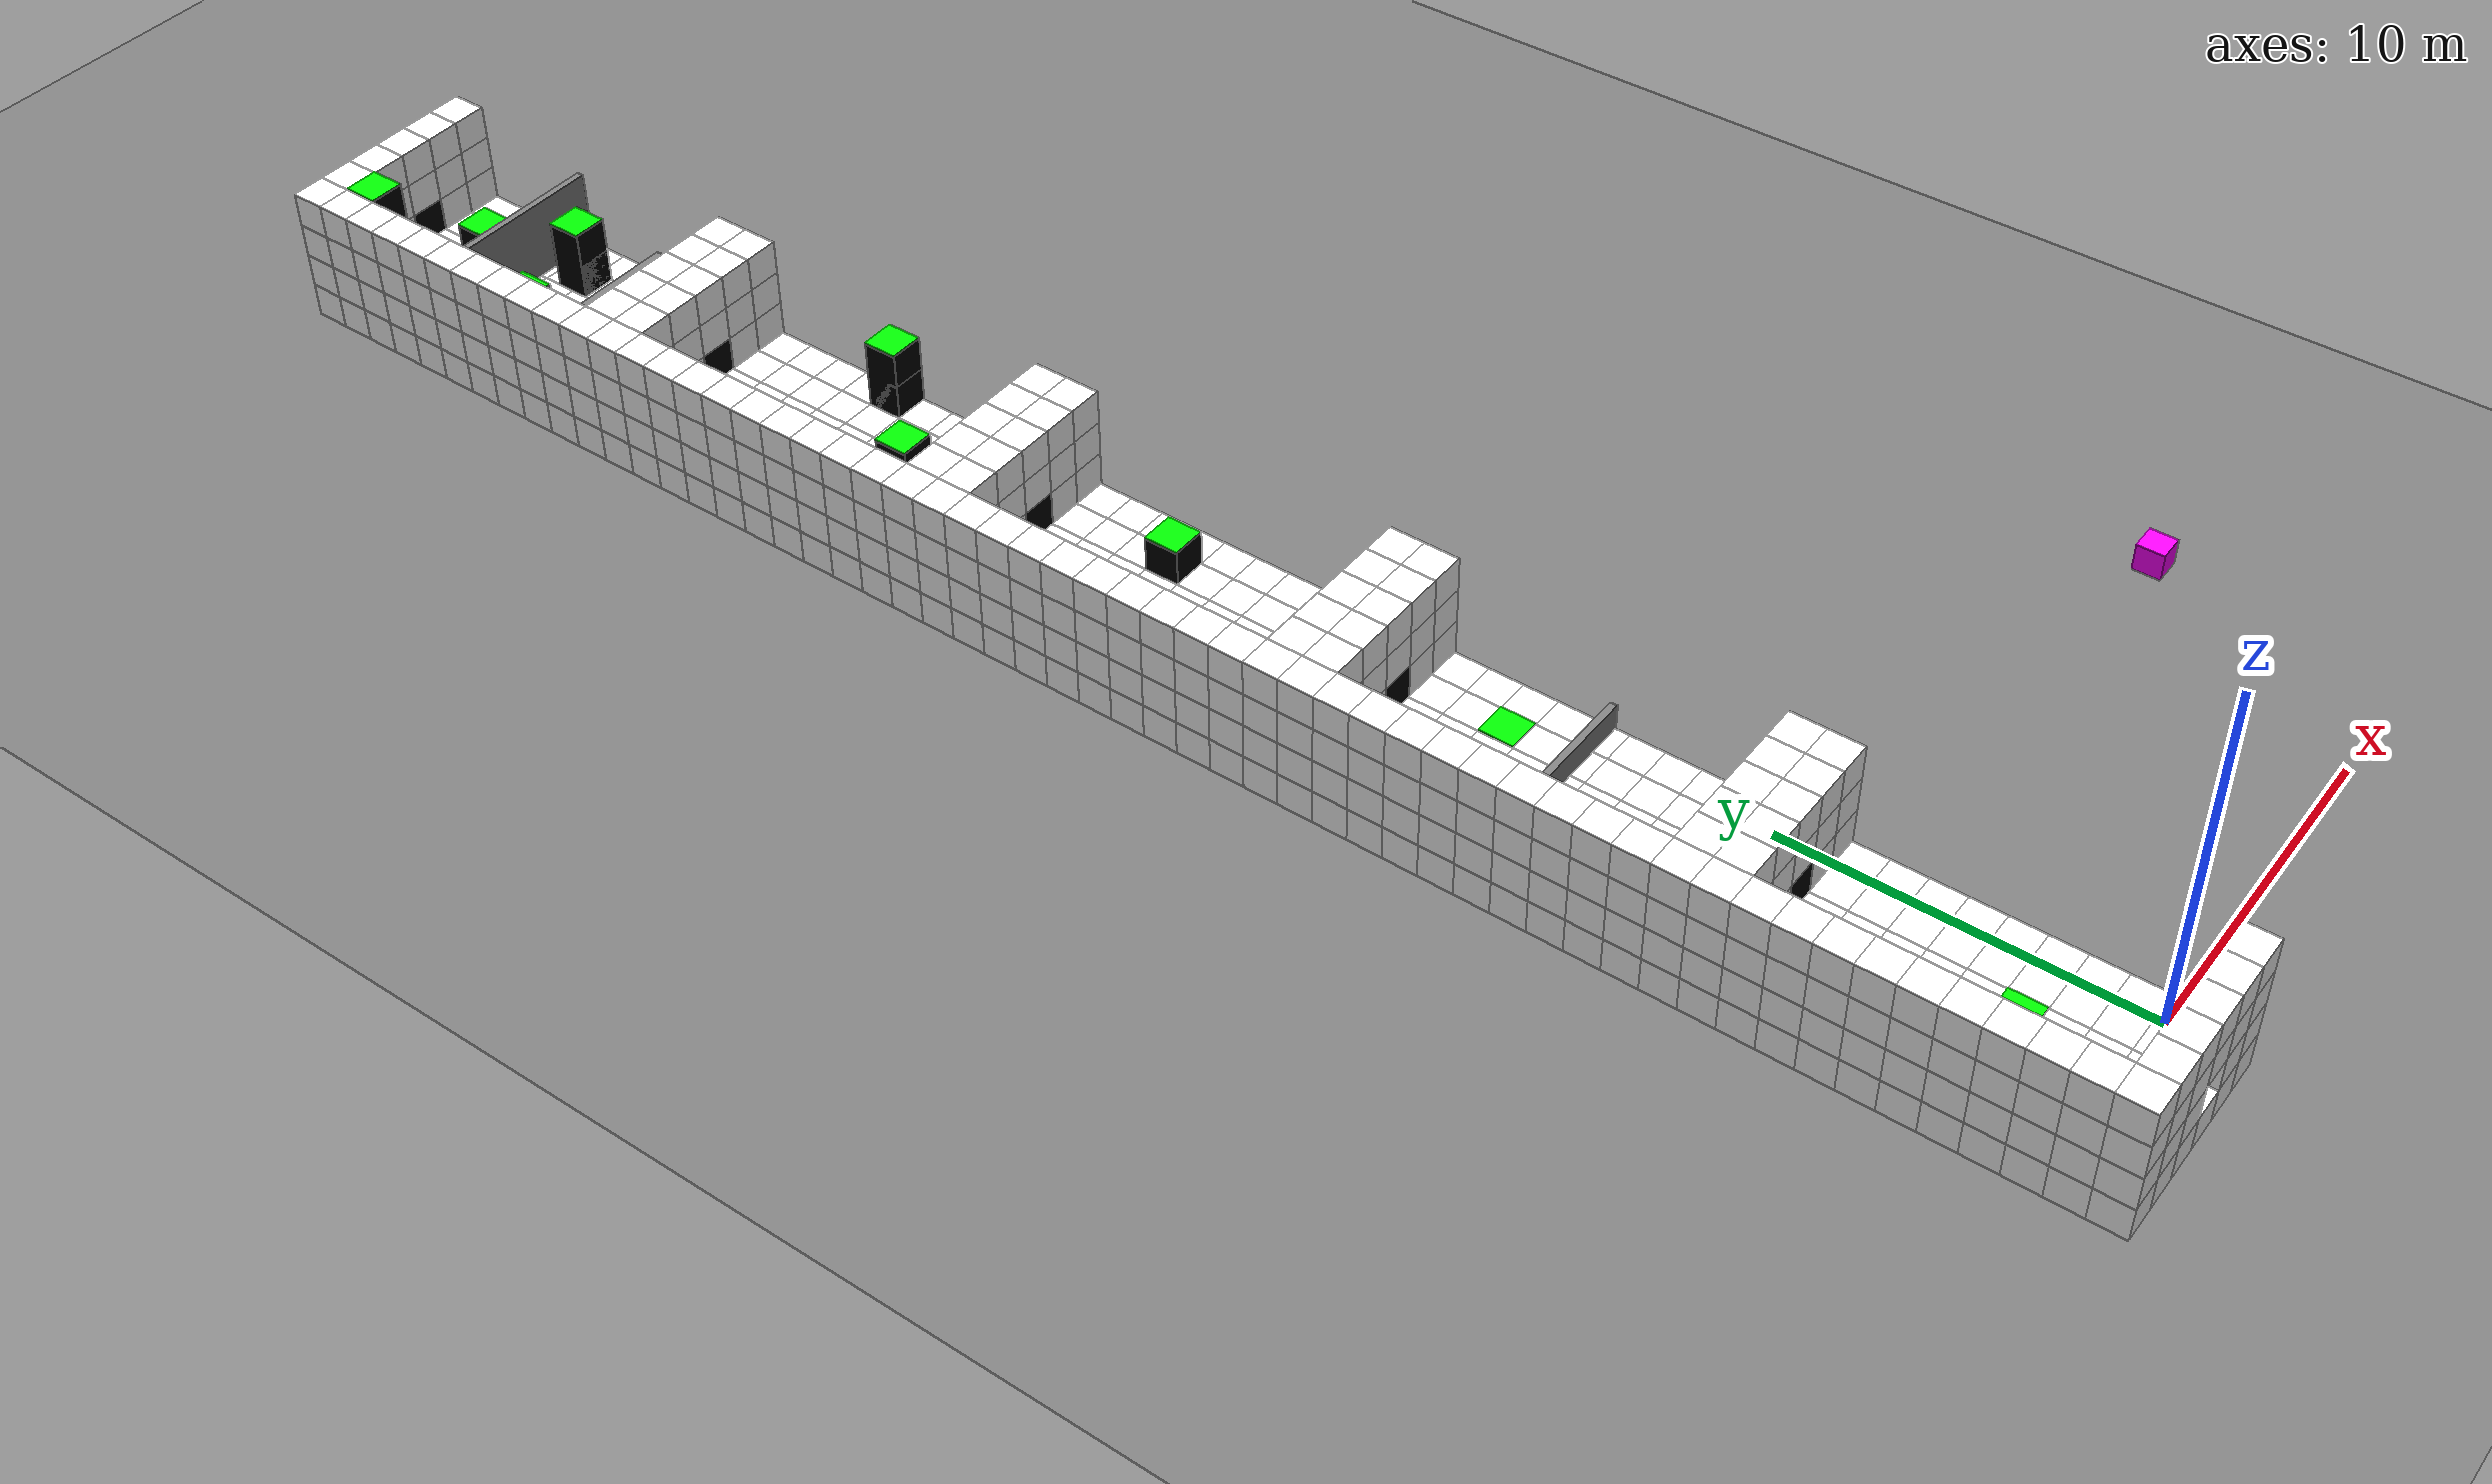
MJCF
<mujoco model="plane_field">
    <compiler angle="radian" coordinate="local" />
    <option gravity="0 0 -9.80 " />
    <worldbody>
        <geom type="plane" name="field" size="40 40 0.01" pos="0 30 -0.5" />
        <body name="Albert" pos="-3 1.5 15">
            <!-- inertial to enable physics -->
            <joint type="free" axis="0 0 0" pos="0 0 0"/>
            <inertial pos="0 0 0" mass="10.0" diaginertia="0.001 0.001 0.001"/>
            <geom name="Albert" type="box" size=".3 .3 .3" pos="0 0 0" rgba="1 0 1 1" />
        </body>

        <body pos=" -5.5 -1.5 0.5">
            <body pos=" 3.0 4.0 0.52" euler=" 0.0 -0.0 0.0">
                <geom type="box" size=".5 .5 .02" pos="0 0 0" rgba="0 1 0 1" />
            </body>
            <body pos=" 0.0 0.0 0.0" euler=" 0.0 -0.0 0.0">
                <geom type="box" size=".5 .5 .5" pos="0 0 0" rgba="1 1 1 1" />
            </body>
            <body pos=" 0.0 1.0 0.0" euler=" 0.0 -0.0 0.0">
                <geom type="box" size=".5 .5 .5" pos="0 0 0" rgba="1 1 1 1" />
            </body>
            <body pos=" 0.0 2.0 0.0" euler=" 0.0 -0.0 0.0">
                <geom type="box" size=".5 .5 .5" pos="0 0 0" rgba="1 1 1 1" />
            </body>
            <body pos=" 0.0 3.0 0.0" euler=" 0.0 -0.0 0.0">
                <geom type="box" size=".5 .5 .5" pos="0 0 0" rgba="1 1 1 1" />
            </body>
            <body pos=" 0.0 4.0 0.0" euler=" 0.0 -0.0 0.0"><geom type="box" size=".5 .5 .5" pos="0 0 0" rgba="1 1 1 1" /></body><body pos=" 0.0 5.0 0.0" euler=" 0.0 -0.0 0.0"><geom type="box" size=".5 .5 .5" pos="0 0 0" rgba="1 1 1 1" /></body><body pos=" 0.0 6.0 0.0" euler=" 0.0 -0.0 0.0"><geom type="box" size=".5 .5 .5" pos="0 0 0" rgba="1 1 1 1" /></body><body pos=" 0.0 7.0 0.0" euler=" 0.0 -0.0 0.0"><geom type="box" size=".5 .5 .5" pos="0 0 0" rgba="1 1 1 1" /></body><body pos=" 0.0 8.0 0.0" euler=" 0.0 -0.0 0.0"><geom type="box" size=".5 .5 .5" pos="0 0 0" rgba="1 1 1 1" /></body><body pos=" 0.0 9.0 0.0" euler=" 0.0 -0.0 0.0"><geom type="box" size=".5 .5 .5" pos="0 0 0" rgba="1 1 1 1" /></body><body pos=" 0.0 10.0 0.0" euler=" 0.0 -0.0 0.0"><geom type="box" size=".5 .5 .5" pos="0 0 0" rgba="1 1 1 1" /></body><body pos=" 1.0 0.0 0.0" euler=" 0.0 -0.0 0.0"><geom type="box" size=".5 .5 .5" pos="0 0 0" rgba="1 1 1 1" /></body><body pos=" 1.0 1.0 0.0" euler=" 0.0 -0.0 0.0"><geom type="box" size=".5 .5 .5" pos="0 0 0" rgba="1 1 1 1" /></body><body pos=" 1.0 2.0 0.0" euler=" 0.0 -0.0 0.0"><geom type="box" size=".5 .5 .5" pos="0 0 0" rgba="1 1 1 1" /></body><body pos=" 1.0 3.0 0.0" euler=" 0.0 -0.0 0.0"><geom type="box" size=".5 .5 .5" pos="0 0 0" rgba="1 1 1 1" /></body><body pos=" 1.0 4.0 0.0" euler=" 0.0 -0.0 0.0"><geom type="box" size=".5 .5 .5" pos="0 0 0" rgba="1 1 1 1" /></body><body pos=" 1.0 5.0 0.0" euler=" 0.0 -0.0 0.0"><geom type="box" size=".5 .5 .5" pos="0 0 0" rgba="1 1 1 1" /></body><body pos=" 1.0 6.0 0.0" euler=" 0.0 -0.0 0.0"><geom type="box" size=".5 .5 .5" pos="0 0 0" rgba="1 1 1 1" /></body><body pos=" 1.0 7.0 0.0" euler=" 0.0 -0.0 0.0"><geom type="box" size=".5 .5 .5" pos="0 0 0" rgba="1 1 1 1" /></body><body pos=" 1.0 8.0 0.0" euler=" 0.0 -0.0 0.0"><geom type="box" size=".5 .5 .5" pos="0 0 0" rgba="1 1 1 1" /></body><body pos=" 1.0 9.0 0.0" euler=" 0.0 -0.0 0.0"><geom type="box" size=".5 .5 .5" pos="0 0 0" rgba="1 1 1 1" /></body><body pos=" 1.0 10.0 0.0" euler=" 0.0 -0.0 0.0"><geom type="box" size=".5 .5 .5" pos="0 0 0" rgba="1 1 1 1" /></body><body pos=" 2.0 0.0 0.0" euler=" 0.0 -0.0 0.0"><geom type="box" size=".5 .5 .5" pos="0 0 0" rgba="1 1 1 1" /></body><body pos=" 2.0 1.0 0.0" euler=" 0.0 -0.0 0.0"><geom type="box" size=".5 .5 .5" pos="0 0 0" rgba="1 1 1 1" /></body><body pos=" 2.0 2.0 0.0" euler=" 0.0 -0.0 0.0"><geom type="box" size=".5 .5 .5" pos="0 0 0" rgba="1 1 1 1" /></body><body pos=" 2.0 3.0 0.0" euler=" 0.0 -0.0 0.0"><geom type="box" size=".5 .5 .5" pos="0 0 0" rgba="1 1 1 1" /></body><body pos=" 2.0 4.0 0.0" euler=" 0.0 -0.0 0.0"><geom type="box" size=".5 .5 .5" pos="0 0 0" rgba="1 1 1 1" /></body><body pos=" 2.0 5.0 0.0" euler=" 0.0 -0.0 0.0"><geom type="box" size=".5 .5 .5" pos="0 0 0" rgba="1 1 1 1" /></body><body pos=" 2.0 6.0 0.0" euler=" 0.0 -0.0 0.0"><geom type="box" size=".5 .5 .5" pos="0 0 0" rgba="1 1 1 1" /></body><body pos=" 2.0 7.0 0.0" euler=" 0.0 -0.0 0.0"><geom type="box" size=".5 .5 .5" pos="0 0 0" rgba="1 1 1 1" /></body><body pos=" 2.0 8.0 0.0" euler=" 0.0 -0.0 0.0"><geom type="box" size=".5 .5 .5" pos="0 0 0" rgba="1 1 1 1" /></body><body pos=" 2.0 9.0 0.0" euler=" 0.0 -0.0 0.0"><geom type="box" size=".5 .5 .5" pos="0 0 0" rgba="1 1 1 1" /></body><body pos=" 2.0 10.0 0.0" euler=" 0.0 -0.0 0.0"><geom type="box" size=".5 .5 .5" pos="0 0 0" rgba="1 1 1 1" /></body><body pos=" 3.0 0.0 0.0" euler=" 0.0 -0.0 0.0"><geom type="box" size=".5 .5 .5" pos="0 0 0" rgba="1 1 1 1" /></body><body pos=" 3.0 1.0 0.0" euler=" 0.0 -0.0 0.0"><geom type="box" size=".5 .5 .5" pos="0 0 0" rgba="1 1 1 1" /></body><body pos=" 3.0 2.0 0.0" euler=" 0.0 -0.0 0.0"><geom type="box" size=".5 .5 .5" pos="0 0 0" rgba="1 1 1 1" /></body><body pos=" 3.0 3.0 0.0" euler=" 0.0 -0.0 0.0"><geom type="box" size=".5 .5 .5" pos="0 0 0" rgba="1 1 1 1" /></body><body pos=" 3.0 4.0 0.0" euler=" 0.0 -0.0 0.0"><geom type="box" size=".5 .5 .5" pos="0 0 0" rgba="1 1 1 1" /></body><body pos=" 3.0 5.0 0.0" euler=" 0.0 -0.0 0.0"><geom type="box" size=".5 .5 .5" pos="0 0 0" rgba="1 1 1 1" /></body><body pos=" 3.0 6.0 0.0" euler=" 0.0 -0.0 0.0"><geom type="box" size=".5 .5 .5" pos="0 0 0" rgba="1 1 1 1" /></body><body pos=" 3.0 7.0 0.0" euler=" 0.0 -0.0 0.0"><geom type="box" size=".5 .5 .5" pos="0 0 0" rgba="1 1 1 1" /></body><body pos=" 3.0 8.0 0.0" euler=" 0.0 -0.0 0.0"><geom type="box" size=".5 .5 .5" pos="0 0 0" rgba="1 1 1 1" /></body><body pos=" 3.0 9.0 0.0" euler=" 0.0 -0.0 0.0"><geom type="box" size=".5 .5 .5" pos="0 0 0" rgba="1 1 1 1" /></body><body pos=" 3.0 10.0 0.0" euler=" 0.0 -0.0 0.0"><geom type="box" size=".5 .5 .5" pos="0 0 0" rgba="1 1 1 1" /></body><body pos=" 4.0 0.0 0.0" euler=" 0.0 -0.0 0.0"><geom type="box" size=".5 .5 .5" pos="0 0 0" rgba="1 1 1 1" /></body><body pos=" 4.0 1.0 0.0" euler=" 0.0 -0.0 0.0"><geom type="box" size=".5 .5 .5" pos="0 0 0" rgba="1 1 1 1" /></body><body pos=" 4.0 2.0 0.0" euler=" 0.0 -0.0 0.0"><geom type="box" size=".5 .5 .5" pos="0 0 0" rgba="1 1 1 1" /></body><body pos=" 4.0 3.0 0.0" euler=" 0.0 -0.0 0.0"><geom type="box" size=".5 .5 .5" pos="0 0 0" rgba="1 1 1 1" /></body><body pos=" 4.0 4.0 0.0" euler=" 0.0 -0.0 0.0"><geom type="box" size=".5 .5 .5" pos="0 0 0" rgba="1 1 1 1" /></body><body pos=" 4.0 5.0 0.0" euler=" 0.0 -0.0 0.0"><geom type="box" size=".5 .5 .5" pos="0 0 0" rgba="1 1 1 1" /></body><body pos=" 4.0 6.0 0.0" euler=" 0.0 -0.0 0.0"><geom type="box" size=".5 .5 .5" pos="0 0 0" rgba="1 1 1 1" /></body><body pos=" 4.0 7.0 0.0" euler=" 0.0 -0.0 0.0"><geom type="box" size=".5 .5 .5" pos="0 0 0" rgba="1 1 1 1" /></body><body pos=" 4.0 8.0 0.0" euler=" 0.0 -0.0 0.0"><geom type="box" size=".5 .5 .5" pos="0 0 0" rgba="1 1 1 1" /></body><body pos=" 4.0 9.0 0.0" euler=" 0.0 -0.0 0.0"><geom type="box" size=".5 .5 .5" pos="0 0 0" rgba="1 1 1 1" /></body><body pos=" 4.0 10.0 0.0" euler=" 0.0 -0.0 0.0"><geom type="box" size=".5 .5 .5" pos="0 0 0" rgba="1 1 1 1" /></body><body pos=" 5.0 0.0 0.0" euler=" 0.0 -0.0 0.0"><geom type="box" size=".5 .5 .5" pos="0 0 0" rgba="1 1 1 1" /></body><body pos=" 5.0 1.0 0.0" euler=" 0.0 -0.0 0.0"><geom type="box" size=".5 .5 .5" pos="0 0 0" rgba="1 1 1 1" /></body><body pos=" 5.0 2.0 0.0" euler=" 0.0 -0.0 0.0"><geom type="box" size=".5 .5 .5" pos="0 0 0" rgba="1 1 1 1" /></body><body pos=" 5.0 3.0 0.0" euler=" 0.0 -0.0 0.0"><geom type="box" size=".5 .5 .5" pos="0 0 0" rgba="1 1 1 1" /></body><body pos=" 5.0 4.0 0.0" euler=" 0.0 -0.0 0.0"><geom type="box" size=".5 .5 .5" pos="0 0 0" rgba="1 1 1 1" /></body><body pos=" 5.0 5.0 0.0" euler=" 0.0 -0.0 0.0"><geom type="box" size=".5 .5 .5" pos="0 0 0" rgba="1 1 1 1" /></body><body pos=" 5.0 6.0 0.0" euler=" 0.0 -0.0 0.0"><geom type="box" size=".5 .5 .5" pos="0 0 0" rgba="1 1 1 1" /></body><body pos=" 5.0 7.0 0.0" euler=" 0.0 -0.0 0.0"><geom type="box" size=".5 .5 .5" pos="0 0 0" rgba="1 1 1 1" /></body><body pos=" 5.0 8.0 0.0" euler=" 0.0 -0.0 0.0"><geom type="box" size=".5 .5 .5" pos="0 0 0" rgba="1 1 1 1" /></body><body pos=" 5.0 9.0 0.0" euler=" 0.0 -0.0 0.0"><geom type="box" size=".5 .5 .5" pos="0 0 0" rgba="1 1 1 1" /></body><body pos=" 5.0 10.0 0.0" euler=" 0.0 -0.0 0.0"><geom type="box" size=".5 .5 .5" pos="0 0 0" rgba="1 1 1 1" /></body><body pos=" 0.0 0.0 1.0" euler=" 0.0 -0.0 0.0"><geom type="box" size=".5 .5 .5" pos="0 0 0" rgba="1 1 1 1" /></body><body pos=" 0.0 0.0 2.0" euler=" 0.0 -0.0 0.0"><geom type="box" size=".5 .5 .5" pos="0 0 0" rgba="1 1 1 1" /></body><body pos=" 0.0 0.0 3.0" euler=" 0.0 -0.0 0.0"><geom type="box" size=".5 .5 .5" pos="0 0 0" rgba="1 1 1 1" /></body><body pos=" 0.0 1.0 1.0" euler=" 0.0 -0.0 0.0"><geom type="box" size=".5 .5 .5" pos="0 0 0" rgba="1 1 1 1" /></body><body pos=" 0.0 1.0 2.0" euler=" 0.0 -0.0 0.0"><geom type="box" size=".5 .5 .5" pos="0 0 0" rgba="1 1 1 1" /></body><body pos=" 0.0 1.0 3.0" euler=" 0.0 -0.0 0.0"><geom type="box" size=".5 .5 .5" pos="0 0 0" rgba="1 1 1 1" /></body><body pos=" 0.0 2.0 1.0" euler=" 0.0 -0.0 0.0"><geom type="box" size=".5 .5 .5" pos="0 0 0" rgba="1 1 1 1" /></body><body pos=" 0.0 2.0 2.0" euler=" 0.0 -0.0 0.0"><geom type="box" size=".5 .5 .5" pos="0 0 0" rgba="1 1 1 1" /></body><body pos=" 0.0 2.0 3.0" euler=" 0.0 -0.0 0.0"><geom type="box" size=".5 .5 .5" pos="0 0 0" rgba="1 1 1 1" /></body><body pos=" 0.0 3.0 1.0" euler=" 0.0 -0.0 0.0"><geom type="box" size=".5 .5 .5" pos="0 0 0" rgba="1 1 1 1" /></body><body pos=" 0.0 3.0 2.0" euler=" 0.0 -0.0 0.0"><geom type="box" size=".5 .5 .5" pos="0 0 0" rgba="1 1 1 1" /></body><body pos=" 0.0 3.0 3.0" euler=" 0.0 -0.0 0.0"><geom type="box" size=".5 .5 .5" pos="0 0 0" rgba="1 1 1 1" /></body><body pos=" 0.0 4.0 1.0" euler=" 0.0 -0.0 0.0"><geom type="box" size=".5 .5 .5" pos="0 0 0" rgba="1 1 1 1" /></body><body pos=" 0.0 4.0 2.0" euler=" 0.0 -0.0 0.0"><geom type="box" size=".5 .5 .5" pos="0 0 0" rgba="1 1 1 1" /></body><body pos=" 0.0 4.0 3.0" euler=" 0.0 -0.0 0.0"><geom type="box" size=".5 .5 .5" pos="0 0 0" rgba="1 1 1 1" /></body><body pos=" 0.0 5.0 1.0" euler=" 0.0 -0.0 0.0"><geom type="box" size=".5 .5 .5" pos="0 0 0" rgba="1 1 1 1" /></body><body pos=" 0.0 5.0 2.0" euler=" 0.0 -0.0 0.0"><geom type="box" size=".5 .5 .5" pos="0 0 0" rgba="1 1 1 1" /></body><body pos=" 0.0 5.0 3.0" euler=" 0.0 -0.0 0.0"><geom type="box" size=".5 .5 .5" pos="0 0 0" rgba="1 1 1 1" /></body><body pos=" 0.0 6.0 1.0" euler=" 0.0 -0.0 0.0"><geom type="box" size=".5 .5 .5" pos="0 0 0" rgba="1 1 1 1" /></body><body pos=" 0.0 6.0 2.0" euler=" 0.0 -0.0 0.0"><geom type="box" size=".5 .5 .5" pos="0 0 0" rgba="1 1 1 1" /></body><body pos=" 0.0 6.0 3.0" euler=" 0.0 -0.0 0.0"><geom type="box" size=".5 .5 .5" pos="0 0 0" rgba="1 1 1 1" /></body><body pos=" 0.0 7.0 1.0" euler=" 0.0 -0.0 0.0"><geom type="box" size=".5 .5 .5" pos="0 0 0" rgba="1 1 1 1" /></body><body pos=" 0.0 7.0 2.0" euler=" 0.0 -0.0 0.0"><geom type="box" size=".5 .5 .5" pos="0 0 0" rgba="1 1 1 1" /></body><body pos=" 0.0 7.0 3.0" euler=" 0.0 -0.0 0.0"><geom type="box" size=".5 .5 .5" pos="0 0 0" rgba="1 1 1 1" /></body><body pos=" 0.0 8.0 1.0" euler=" 0.0 -0.0 0.0"><geom type="box" size=".5 .5 .5" pos="0 0 0" rgba="1 1 1 1" /></body><body pos=" 0.0 8.0 2.0" euler=" 0.0 -0.0 0.0"><geom type="box" size=".5 .5 .5" pos="0 0 0" rgba="1 1 1 1" /></body><body pos=" 0.0 8.0 3.0" euler=" 0.0 -0.0 0.0"><geom type="box" size=".5 .5 .5" pos="0 0 0" rgba="1 1 1 1" /></body><body pos=" 0.0 9.0 1.0" euler=" 0.0 -0.0 0.0"><geom type="box" size=".5 .5 .5" pos="0 0 0" rgba="1 1 1 1" /></body><body pos=" 0.0 9.0 2.0" euler=" 0.0 -0.0 0.0"><geom type="box" size=".5 .5 .5" pos="0 0 0" rgba="1 1 1 1" /></body><body pos=" 0.0 9.0 3.0" euler=" 0.0 -0.0 0.0"><geom type="box" size=".5 .5 .5" pos="0 0 0" rgba="1 1 1 1" /></body><body pos=" 0.0 10.0 1.0" euler=" 0.0 -0.0 0.0"><geom type="box" size=".5 .5 .5" pos="0 0 0" rgba="1 1 1 1" /></body><body pos=" 0.0 10.0 2.0" euler=" 0.0 -0.0 0.0"><geom type="box" size=".5 .5 .5" pos="0 0 0" rgba="1 1 1 1" /></body><body pos=" 0.0 10.0 3.0" euler=" 0.0 -0.0 0.0"><geom type="box" size=".5 .5 .5" pos="0 0 0" rgba="1 1 1 1" /></body><body pos=" 1.0 0.0 1.0" euler=" 0.0 -0.0 0.0"><geom type="box" size=".5 .5 .5" pos="0 0 0" rgba="1 1 1 1" /></body><body pos=" 1.0 0.0 2.0" euler=" 0.0 -0.0 0.0"><geom type="box" size=".5 .5 .5" pos="0 0 0" rgba="1 1 1 1" /></body><body pos=" 1.0 0.0 3.0" euler=" 0.0 -0.0 0.0"><geom type="box" size=".5 .5 .5" pos="0 0 0" rgba="1 1 1 1" /></body><body pos=" 1.0 10.0 1.0" euler=" 0.0 -0.0 0.0"><geom type="box" size=".5 .5 .5" pos="0 0 0" rgba="1 1 1 1" /></body><body pos=" 1.0 10.0 2.0" euler=" 0.0 -0.0 0.0"><geom type="box" size=".5 .5 .5" pos="0 0 0" rgba="1 1 1 1" /></body><body pos=" 1.0 10.0 3.0" euler=" 0.0 -0.0 0.0"><geom type="box" size=".5 .5 .5" pos="0 0 0" rgba="1 1 1 1" /></body><body pos=" 2.0 0.0 1.0" euler=" 0.0 -0.0 0.0"><geom type="box" size=".5 .5 .5" pos="0 0 0" rgba="1 1 1 1" /></body><body pos=" 2.0 0.0 2.0" euler=" 0.0 -0.0 0.0"><geom type="box" size=".5 .5 .5" pos="0 0 0" rgba="1 1 1 1" /></body><body pos=" 2.0 0.0 3.0" euler=" 0.0 -0.0 0.0"><geom type="box" size=".5 .5 .5" pos="0 0 0" rgba="1 1 1 1" /></body><body pos=" 2.0 10.0 1.0" euler=" 0.0 -0.0 0.0"><geom type="box" size=".5 .5 .5" pos="0 0 0" rgba="1 1 1 1" /></body><body pos=" 2.0 10.0 2.0" euler=" 0.0 -0.0 0.0"><geom type="box" size=".5 .5 .5" pos="0 0 0" rgba="1 1 1 1" /></body><body pos=" 2.0 10.0 3.0" euler=" 0.0 -0.0 0.0"><geom type="box" size=".5 .5 .5" pos="0 0 0" rgba="1 1 1 1" /></body><body pos=" 3.0 0.0 2.0" euler=" 0.0 -0.0 0.0"><geom type="box" size=".5 .5 .5" pos="0 0 0" rgba="1 1 1 1" /></body><body pos=" 3.0 0.0 3.0" euler=" 0.0 -0.0 0.0"><geom type="box" size=".5 .5 .5" pos="0 0 0" rgba="1 1 1 1" /></body><body pos=" 3.0 10.0 2.0" euler=" 0.0 -0.0 0.0"><geom type="box" size=".5 .5 .5" pos="0 0 0" rgba="1 1 1 1" /></body><body pos=" 3.0 10.0 3.0" euler=" 0.0 -0.0 0.0"><geom type="box" size=".5 .5 .5" pos="0 0 0" rgba="1 1 1 1" /></body><body pos=" 4.0 0.0 1.0" euler=" 0.0 -0.0 0.0"><geom type="box" size=".5 .5 .5" pos="0 0 0" rgba="1 1 1 1" /></body><body pos=" 4.0 0.0 2.0" euler=" 0.0 -0.0 0.0"><geom type="box" size=".5 .5 .5" pos="0 0 0" rgba="1 1 1 1" /></body><body pos=" 4.0 0.0 3.0" euler=" 0.0 -0.0 0.0"><geom type="box" size=".5 .5 .5" pos="0 0 0" rgba="1 1 1 1" /></body><body pos=" 4.0 10.0 1.0" euler=" 0.0 -0.0 0.0"><geom type="box" size=".5 .5 .5" pos="0 0 0" rgba="1 1 1 1" /></body><body pos=" 4.0 10.0 2.0" euler=" 0.0 -0.0 0.0"><geom type="box" size=".5 .5 .5" pos="0 0 0" rgba="1 1 1 1" /></body><body pos=" 4.0 10.0 3.0" euler=" 0.0 -0.0 0.0"><geom type="box" size=".5 .5 .5" pos="0 0 0" rgba="1 1 1 1" /></body><body pos=" 5.0 0.0 1.0" euler=" 0.0 -0.0 0.0"><geom type="box" size=".5 .5 .5" pos="0 0 0" rgba="1 1 1 1" /></body><body pos=" 5.0 0.0 2.0" euler=" 0.0 -0.0 0.0"><geom type="box" size=".5 .5 .5" pos="0 0 0" rgba="1 1 1 1" /></body><body pos=" 5.0 0.0 3.0" euler=" 0.0 -0.0 0.0"><geom type="box" size=".5 .5 .5" pos="0 0 0" rgba="1 1 1 1" /></body><body pos=" 5.0 10.0 1.0" euler=" 0.0 -0.0 0.0"><geom type="box" size=".5 .5 .5" pos="0 0 0" rgba="1 1 1 1" /></body><body pos=" 5.0 10.0 2.0" euler=" 0.0 -0.0 0.0"><geom type="box" size=".5 .5 .5" pos="0 0 0" rgba="1 1 1 1" /></body><body pos=" 5.0 10.0 3.0" euler=" 0.0 -0.0 0.0"><geom type="box" size=".5 .5 .5" pos="0 0 0" rgba="1 1 1 1" /></body><body pos=" 3.0 10.0 1.0" euler=" 0.0 -0.0 0.0"><geom type="box" size=".5 .5 .5" pos="0 0 0" rgba="0 0 0 1" /></body></body><body pos=" -5.5 9.5 0.5"><body pos=" 2.0 3.0 0.52" euler=" 0.0 -0.0 0.0"><geom type="box" size=".5 .5 .02" pos="0 0 0" rgba="0 1 0 1" /></body><body pos=" 4.0 7.0 0.52" euler=" 0.0 -0.0 0.0"><geom type="box" size=".5 .5 .02" pos="0 0 0" rgba="0 1 0 1" /></body><body pos=" 0.0 0.0 0.0" euler=" 0.0 -0.0 0.0"><geom type="box" size=".5 .5 .5" pos="0 0 0" rgba="1 1 1 1" /></body><body pos=" 0.0 1.0 0.0" euler=" 0.0 -0.0 0.0"><geom type="box" size=".5 .5 .5" pos="0 0 0" rgba="1 1 1 1" /></body><body pos=" 0.0 2.0 0.0" euler=" 0.0 -0.0 0.0"><geom type="box" size=".5 .5 .5" pos="0 0 0" rgba="1 1 1 1" /></body><body pos=" 0.0 3.0 0.0" euler=" 0.0 -0.0 0.0"><geom type="box" size=".5 .5 .5" pos="0 0 0" rgba="1 1 1 1" /></body><body pos=" 0.0 4.0 0.0" euler=" 0.0 -0.0 0.0"><geom type="box" size=".5 .5 .5" pos="0 0 0" rgba="1 1 1 1" /></body><body pos=" 0.0 5.0 0.0" euler=" 0.0 -0.0 0.0"><geom type="box" size=".5 .5 .5" pos="0 0 0" rgba="1 1 1 1" /></body><body pos=" 0.0 6.0 0.0" euler=" 0.0 -0.0 0.0"><geom type="box" size=".5 .5 .5" pos="0 0 0" rgba="1 1 1 1" /></body><body pos=" 0.0 7.0 0.0" euler=" 0.0 -0.0 0.0"><geom type="box" size=".5 .5 .5" pos="0 0 0" rgba="1 1 1 1" /></body><body pos=" 0.0 8.0 0.0" euler=" 0.0 -0.0 0.0"><geom type="box" size=".5 .5 .5" pos="0 0 0" rgba="1 1 1 1" /></body><body pos=" 0.0 9.0 0.0" euler=" 0.0 -0.0 0.0"><geom type="box" size=".5 .5 .5" pos="0 0 0" rgba="1 1 1 1" /></body><body pos=" 0.0 10.0 0.0" euler=" 0.0 -0.0 0.0"><geom type="box" size=".5 .5 .5" pos="0 0 0" rgba="1 1 1 1" /></body><body pos=" 1.0 0.0 0.0" euler=" 0.0 -0.0 0.0"><geom type="box" size=".5 .5 .5" pos="0 0 0" rgba="1 1 1 1" /></body><body pos=" 1.0 1.0 0.0" euler=" 0.0 -0.0 0.0"><geom type="box" size=".5 .5 .5" pos="0 0 0" rgba="1 1 1 1" /></body><body pos=" 1.0 2.0 0.0" euler=" 0.0 -0.0 0.0"><geom type="box" size=".5 .5 .5" pos="0 0 0" rgba="1 1 1 1" /></body><body pos=" 1.0 3.0 0.0" euler=" 0.0 -0.0 0.0"><geom type="box" size=".5 .5 .5" pos="0 0 0" rgba="1 1 1 1" /></body><body pos=" 1.0 4.0 0.0" euler=" 0.0 -0.0 0.0"><geom type="box" size=".5 .5 .5" pos="0 0 0" rgba="1 1 1 1" /></body><body pos=" 1.0 5.0 0.0" euler=" 0.0 -0.0 0.0"><geom type="box" size=".5 .5 .5" pos="0 0 0" rgba="1 1 1 1" /></body><body pos=" 1.0 6.0 0.0" euler=" 0.0 -0.0 0.0"><geom type="box" size=".5 .5 .5" pos="0 0 0" rgba="1 1 1 1" /></body><body pos=" 1.0 7.0 0.0" euler=" 0.0 -0.0 0.0"><geom type="box" size=".5 .5 .5" pos="0 0 0" rgba="1 1 1 1" /></body><body pos=" 1.0 8.0 0.0" euler=" 0.0 -0.0 0.0"><geom type="box" size=".5 .5 .5" pos="0 0 0" rgba="1 1 1 1" /></body><body pos=" 1.0 9.0 0.0" euler=" 0.0 -0.0 0.0"><geom type="box" size=".5 .5 .5" pos="0 0 0" rgba="1 1 1 1" /></body><body pos=" 1.0 10.0 0.0" euler=" 0.0 -0.0 0.0"><geom type="box" size=".5 .5 .5" pos="0 0 0" rgba="1 1 1 1" /></body><body pos=" 2.0 0.0 0.0" euler=" 0.0 -0.0 0.0"><geom type="box" size=".5 .5 .5" pos="0 0 0" rgba="1 1 1 1" /></body><body pos=" 2.0 1.0 0.0" euler=" 0.0 -0.0 0.0"><geom type="box" size=".5 .5 .5" pos="0 0 0" rgba="1 1 1 1" /></body><body pos=" 2.0 2.0 0.0" euler=" 0.0 -0.0 0.0"><geom type="box" size=".5 .5 .5" pos="0 0 0" rgba="1 1 1 1" /></body><body pos=" 2.0 3.0 0.0" euler=" 0.0 -0.0 0.0"><geom type="box" size=".5 .5 .5" pos="0 0 0" rgba="1 1 1 1" /></body><body pos=" 2.0 4.0 0.0" euler=" 0.0 -0.0 0.0"><geom type="box" size=".5 .5 .5" pos="0 0 0" rgba="1 1 1 1" /></body><body pos=" 2.0 5.0 0.0" euler=" 0.0 -0.0 0.0"><geom type="box" size=".5 .5 .5" pos="0 0 0" rgba="1 1 1 1" /></body><body pos=" 2.0 6.0 0.0" euler=" 0.0 -0.0 0.0"><geom type="box" size=".5 .5 .5" pos="0 0 0" rgba="1 1 1 1" /></body><body pos=" 2.0 7.0 0.0" euler=" 0.0 -0.0 0.0"><geom type="box" size=".5 .5 .5" pos="0 0 0" rgba="1 1 1 1" /></body><body pos=" 2.0 8.0 0.0" euler=" 0.0 -0.0 0.0"><geom type="box" size=".5 .5 .5" pos="0 0 0" rgba="1 1 1 1" /></body><body pos=" 2.0 9.0 0.0" euler=" 0.0 -0.0 0.0"><geom type="box" size=".5 .5 .5" pos="0 0 0" rgba="1 1 1 1" /></body><body pos=" 2.0 10.0 0.0" euler=" 0.0 -0.0 0.0"><geom type="box" size=".5 .5 .5" pos="0 0 0" rgba="1 1 1 1" /></body><body pos=" 3.0 0.0 0.0" euler=" 0.0 -0.0 0.0"><geom type="box" size=".5 .5 .5" pos="0 0 0" rgba="1 1 1 1" /></body><body pos=" 3.0 1.0 0.0" euler=" 0.0 -0.0 0.0"><geom type="box" size=".5 .5 .5" pos="0 0 0" rgba="1 1 1 1" /></body><body pos=" 3.0 2.0 0.0" euler=" 0.0 -0.0 0.0"><geom type="box" size=".5 .5 .5" pos="0 0 0" rgba="1 1 1 1" /></body><body pos=" 3.0 3.0 0.0" euler=" 0.0 -0.0 0.0"><geom type="box" size=".5 .5 .5" pos="0 0 0" rgba="1 1 1 1" /></body><body pos=" 3.0 4.0 0.0" euler=" 0.0 -0.0 0.0"><geom type="box" size=".5 .5 .5" pos="0 0 0" rgba="1 1 1 1" /></body><body pos=" 3.0 5.0 0.0" euler=" 0.0 -0.0 0.0"><geom type="box" size=".5 .5 .5" pos="0 0 0" rgba="1 1 1 1" /></body><body pos=" 3.0 6.0 0.0" euler=" 0.0 -0.0 0.0"><geom type="box" size=".5 .5 .5" pos="0 0 0" rgba="1 1 1 1" /></body><body pos=" 3.0 7.0 0.0" euler=" 0.0 -0.0 0.0"><geom type="box" size=".5 .5 .5" pos="0 0 0" rgba="1 1 1 1" /></body><body pos=" 3.0 8.0 0.0" euler=" 0.0 -0.0 0.0"><geom type="box" size=".5 .5 .5" pos="0 0 0" rgba="1 1 1 1" /></body><body pos=" 3.0 9.0 0.0" euler=" 0.0 -0.0 0.0"><geom type="box" size=".5 .5 .5" pos="0 0 0" rgba="1 1 1 1" /></body><body pos=" 3.0 10.0 0.0" euler=" 0.0 -0.0 0.0"><geom type="box" size=".5 .5 .5" pos="0 0 0" rgba="1 1 1 1" /></body><body pos=" 4.0 0.0 0.0" euler=" 0.0 -0.0 0.0"><geom type="box" size=".5 .5 .5" pos="0 0 0" rgba="1 1 1 1" /></body><body pos=" 4.0 1.0 0.0" euler=" 0.0 -0.0 0.0"><geom type="box" size=".5 .5 .5" pos="0 0 0" rgba="1 1 1 1" /></body><body pos=" 4.0 2.0 0.0" euler=" 0.0 -0.0 0.0"><geom type="box" size=".5 .5 .5" pos="0 0 0" rgba="1 1 1 1" /></body><body pos=" 4.0 3.0 0.0" euler=" 0.0 -0.0 0.0"><geom type="box" size=".5 .5 .5" pos="0 0 0" rgba="1 1 1 1" /></body><body pos=" 4.0 4.0 0.0" euler=" 0.0 -0.0 0.0"><geom type="box" size=".5 .5 .5" pos="0 0 0" rgba="1 1 1 1" /></body><body pos=" 4.0 5.0 0.0" euler=" 0.0 -0.0 0.0"><geom type="box" size=".5 .5 .5" pos="0 0 0" rgba="1 1 1 1" /></body><body pos=" 4.0 6.0 0.0" euler=" 0.0 -0.0 0.0"><geom type="box" size=".5 .5 .5" pos="0 0 0" rgba="1 1 1 1" /></body><body pos=" 4.0 7.0 0.0" euler=" 0.0 -0.0 0.0"><geom type="box" size=".5 .5 .5" pos="0 0 0" rgba="1 1 1 1" /></body><body pos=" 4.0 8.0 0.0" euler=" 0.0 -0.0 0.0"><geom type="box" size=".5 .5 .5" pos="0 0 0" rgba="1 1 1 1" /></body><body pos=" 4.0 9.0 0.0" euler=" 0.0 -0.0 0.0"><geom type="box" size=".5 .5 .5" pos="0 0 0" rgba="1 1 1 1" /></body><body pos=" 4.0 10.0 0.0" euler=" 0.0 -0.0 0.0"><geom type="box" size=".5 .5 .5" pos="0 0 0" rgba="1 1 1 1" /></body><body pos=" 5.0 0.0 0.0" euler=" 0.0 -0.0 0.0"><geom type="box" size=".5 .5 .5" pos="0 0 0" rgba="1 1 1 1" /></body><body pos=" 5.0 1.0 0.0" euler=" 0.0 -0.0 0.0"><geom type="box" size=".5 .5 .5" pos="0 0 0" rgba="1 1 1 1" /></body><body pos=" 5.0 2.0 0.0" euler=" 0.0 -0.0 0.0"><geom type="box" size=".5 .5 .5" pos="0 0 0" rgba="1 1 1 1" /></body><body pos=" 5.0 3.0 0.0" euler=" 0.0 -0.0 0.0"><geom type="box" size=".5 .5 .5" pos="0 0 0" rgba="1 1 1 1" /></body><body pos=" 5.0 4.0 0.0" euler=" 0.0 -0.0 0.0"><geom type="box" size=".5 .5 .5" pos="0 0 0" rgba="1 1 1 1" /></body><body pos=" 5.0 5.0 0.0" euler=" 0.0 -0.0 0.0"><geom type="box" size=".5 .5 .5" pos="0 0 0" rgba="1 1 1 1" /></body><body pos=" 5.0 6.0 0.0" euler=" 0.0 -0.0 0.0"><geom type="box" size=".5 .5 .5" pos="0 0 0" rgba="1 1 1 1" /></body><body pos=" 5.0 7.0 0.0" euler=" 0.0 -0.0 0.0"><geom type="box" size=".5 .5 .5" pos="0 0 0" rgba="1 1 1 1" /></body><body pos=" 5.0 8.0 0.0" euler=" 0.0 -0.0 0.0"><geom type="box" size=".5 .5 .5" pos="0 0 0" rgba="1 1 1 1" /></body><body pos=" 5.0 9.0 0.0" euler=" 0.0 -0.0 0.0"><geom type="box" size=".5 .5 .5" pos="0 0 0" rgba="1 1 1 1" /></body><body pos=" 5.0 10.0 0.0" euler=" 0.0 -0.0 0.0"><geom type="box" size=".5 .5 .5" pos="0 0 0" rgba="1 1 1 1" /></body><body pos=" 0.0 0.0 1.0" euler=" 0.0 -0.0 0.0"><geom type="box" size=".5 .5 .5" pos="0 0 0" rgba="1 1 1 1" /></body><body pos=" 0.0 0.0 2.0" euler=" 0.0 -0.0 0.0"><geom type="box" size=".5 .5 .5" pos="0 0 0" rgba="1 1 1 1" /></body><body pos=" 0.0 0.0 3.0" euler=" 0.0 -0.0 0.0"><geom type="box" size=".5 .5 .5" pos="0 0 0" rgba="1 1 1 1" /></body><body pos=" 0.0 1.0 1.0" euler=" 0.0 -0.0 0.0"><geom type="box" size=".5 .5 .5" pos="0 0 0" rgba="1 1 1 1" /></body><body pos=" 0.0 1.0 2.0" euler=" 0.0 -0.0 0.0"><geom type="box" size=".5 .5 .5" pos="0 0 0" rgba="1 1 1 1" /></body><body pos=" 0.0 1.0 3.0" euler=" 0.0 -0.0 0.0"><geom type="box" size=".5 .5 .5" pos="0 0 0" rgba="1 1 1 1" /></body><body pos=" 0.0 2.0 1.0" euler=" 0.0 -0.0 0.0"><geom type="box" size=".5 .5 .5" pos="0 0 0" rgba="1 1 1 1" /></body><body pos=" 0.0 2.0 2.0" euler=" 0.0 -0.0 0.0"><geom type="box" size=".5 .5 .5" pos="0 0 0" rgba="1 1 1 1" /></body><body pos=" 0.0 2.0 3.0" euler=" 0.0 -0.0 0.0"><geom type="box" size=".5 .5 .5" pos="0 0 0" rgba="1 1 1 1" /></body><body pos=" 0.0 3.0 1.0" euler=" 0.0 -0.0 0.0"><geom type="box" size=".5 .5 .5" pos="0 0 0" rgba="1 1 1 1" /></body><body pos=" 0.0 3.0 2.0" euler=" 0.0 -0.0 0.0"><geom type="box" size=".5 .5 .5" pos="0 0 0" rgba="1 1 1 1" /></body><body pos=" 0.0 3.0 3.0" euler=" 0.0 -0.0 0.0"><geom type="box" size=".5 .5 .5" pos="0 0 0" rgba="1 1 1 1" /></body><body pos=" 0.0 4.0 1.0" euler=" 0.0 -0.0 0.0"><geom type="box" size=".5 .5 .5" pos="0 0 0" rgba="1 1 1 1" /></body><body pos=" 0.0 4.0 2.0" euler=" 0.0 -0.0 0.0"><geom type="box" size=".5 .5 .5" pos="0 0 0" rgba="1 1 1 1" /></body><body pos=" 0.0 4.0 3.0" euler=" 0.0 -0.0 0.0"><geom type="box" size=".5 .5 .5" pos="0 0 0" rgba="1 1 1 1" /></body><body pos=" 0.0 5.0 1.0" euler=" 0.0 -0.0 0.0"><geom type="box" size=".5 .5 .5" pos="0 0 0" rgba="1 1 1 1" /></body><body pos=" 0.0 5.0 2.0" euler=" 0.0 -0.0 0.0"><geom type="box" size=".5 .5 .5" pos="0 0 0" rgba="1 1 1 1" /></body><body pos=" 0.0 5.0 3.0" euler=" 0.0 -0.0 0.0"><geom type="box" size=".5 .5 .5" pos="0 0 0" rgba="1 1 1 1" /></body><body pos=" 0.0 6.0 1.0" euler=" 0.0 -0.0 0.0"><geom type="box" size=".5 .5 .5" pos="0 0 0" rgba="1 1 1 1" /></body><body pos=" 0.0 6.0 2.0" euler=" 0.0 -0.0 0.0"><geom type="box" size=".5 .5 .5" pos="0 0 0" rgba="1 1 1 1" /></body><body pos=" 0.0 6.0 3.0" euler=" 0.0 -0.0 0.0"><geom type="box" size=".5 .5 .5" pos="0 0 0" rgba="1 1 1 1" /></body><body pos=" 0.0 7.0 1.0" euler=" 0.0 -0.0 0.0"><geom type="box" size=".5 .5 .5" pos="0 0 0" rgba="1 1 1 1" /></body><body pos=" 0.0 7.0 2.0" euler=" 0.0 -0.0 0.0"><geom type="box" size=".5 .5 .5" pos="0 0 0" rgba="1 1 1 1" /></body><body pos=" 0.0 7.0 3.0" euler=" 0.0 -0.0 0.0"><geom type="box" size=".5 .5 .5" pos="0 0 0" rgba="1 1 1 1" /></body><body pos=" 0.0 8.0 1.0" euler=" 0.0 -0.0 0.0"><geom type="box" size=".5 .5 .5" pos="0 0 0" rgba="1 1 1 1" /></body><body pos=" 0.0 8.0 2.0" euler=" 0.0 -0.0 0.0"><geom type="box" size=".5 .5 .5" pos="0 0 0" rgba="1 1 1 1" /></body><body pos=" 0.0 8.0 3.0" euler=" 0.0 -0.0 0.0"><geom type="box" size=".5 .5 .5" pos="0 0 0" rgba="1 1 1 1" /></body><body pos=" 0.0 9.0 1.0" euler=" 0.0 -0.0 0.0"><geom type="box" size=".5 .5 .5" pos="0 0 0" rgba="1 1 1 1" /></body><body pos=" 0.0 9.0 2.0" euler=" 0.0 -0.0 0.0"><geom type="box" size=".5 .5 .5" pos="0 0 0" rgba="1 1 1 1" /></body><body pos=" 0.0 9.0 3.0" euler=" 0.0 -0.0 0.0"><geom type="box" size=".5 .5 .5" pos="0 0 0" rgba="1 1 1 1" /></body><body pos=" 0.0 10.0 1.0" euler=" 0.0 -0.0 0.0"><geom type="box" size=".5 .5 .5" pos="0 0 0" rgba="1 1 1 1" /></body><body pos=" 0.0 10.0 2.0" euler=" 0.0 -0.0 0.0"><geom type="box" size=".5 .5 .5" pos="0 0 0" rgba="1 1 1 1" /></body><body pos=" 0.0 10.0 3.0" euler=" 0.0 -0.0 0.0"><geom type="box" size=".5 .5 .5" pos="0 0 0" rgba="1 1 1 1" /></body><body pos=" 1.0 0.0 1.0" euler=" 0.0 -0.0 0.0"><geom type="box" size=".5 .5 .5" pos="0 0 0" rgba="1 1 1 1" /></body><body pos=" 1.0 0.0 2.0" euler=" 0.0 -0.0 0.0"><geom type="box" size=".5 .5 .5" pos="0 0 0" rgba="1 1 1 1" /></body><body pos=" 1.0 0.0 3.0" euler=" 0.0 -0.0 0.0"><geom type="box" size=".5 .5 .5" pos="0 0 0" rgba="1 1 1 1" /></body><body pos=" 1.0 10.0 1.0" euler=" 0.0 -0.0 0.0"><geom type="box" size=".5 .5 .5" pos="0 0 0" rgba="1 1 1 1" /></body><body pos=" 1.0 10.0 2.0" euler=" 0.0 -0.0 0.0"><geom type="box" size=".5 .5 .5" pos="0 0 0" rgba="1 1 1 1" /></body><body pos=" 1.0 10.0 3.0" euler=" 0.0 -0.0 0.0"><geom type="box" size=".5 .5 .5" pos="0 0 0" rgba="1 1 1 1" /></body><body pos=" 2.0 0.0 1.0" euler=" 0.0 -0.0 0.0"><geom type="box" size=".5 .5 .5" pos="0 0 0" rgba="1 1 1 1" /></body><body pos=" 2.0 0.0 2.0" euler=" 0.0 -0.0 0.0"><geom type="box" size=".5 .5 .5" pos="0 0 0" rgba="1 1 1 1" /></body><body pos=" 2.0 0.0 3.0" euler=" 0.0 -0.0 0.0"><geom type="box" size=".5 .5 .5" pos="0 0 0" rgba="1 1 1 1" /></body><body pos=" 2.0 10.0 1.0" euler=" 0.0 -0.0 0.0"><geom type="box" size=".5 .5 .5" pos="0 0 0" rgba="1 1 1 1" /></body><body pos=" 2.0 10.0 2.0" euler=" 0.0 -0.0 0.0"><geom type="box" size=".5 .5 .5" pos="0 0 0" rgba="1 1 1 1" /></body><body pos=" 2.0 10.0 3.0" euler=" 0.0 -0.0 0.0"><geom type="box" size=".5 .5 .5" pos="0 0 0" rgba="1 1 1 1" /></body><body pos=" 3.0 0.0 2.0" euler=" 0.0 -0.0 0.0"><geom type="box" size=".5 .5 .5" pos="0 0 0" rgba="1 1 1 1" /></body><body pos=" 3.0 0.0 3.0" euler=" 0.0 -0.0 0.0"><geom type="box" size=".5 .5 .5" pos="0 0 0" rgba="1 1 1 1" /></body><body pos=" 3.0 10.0 2.0" euler=" 0.0 -0.0 0.0"><geom type="box" size=".5 .5 .5" pos="0 0 0" rgba="1 1 1 1" /></body><body pos=" 3.0 10.0 3.0" euler=" 0.0 -0.0 0.0"><geom type="box" size=".5 .5 .5" pos="0 0 0" rgba="1 1 1 1" /></body><body pos=" 4.0 0.0 1.0" euler=" 0.0 -0.0 0.0"><geom type="box" size=".5 .5 .5" pos="0 0 0" rgba="1 1 1 1" /></body><body pos=" 4.0 0.0 2.0" euler=" 0.0 -0.0 0.0"><geom type="box" size=".5 .5 .5" pos="0 0 0" rgba="1 1 1 1" /></body><body pos=" 4.0 0.0 3.0" euler=" 0.0 -0.0 0.0"><geom type="box" size=".5 .5 .5" pos="0 0 0" rgba="1 1 1 1" /></body><body pos=" 4.0 10.0 1.0" euler=" 0.0 -0.0 0.0"><geom type="box" size=".5 .5 .5" pos="0 0 0" rgba="1 1 1 1" /></body><body pos=" 4.0 10.0 2.0" euler=" 0.0 -0.0 0.0"><geom type="box" size=".5 .5 .5" pos="0 0 0" rgba="1 1 1 1" /></body><body pos=" 4.0 10.0 3.0" euler=" 0.0 -0.0 0.0"><geom type="box" size=".5 .5 .5" pos="0 0 0" rgba="1 1 1 1" /></body><body pos=" 5.0 0.0 1.0" euler=" 0.0 -0.0 0.0"><geom type="box" size=".5 .5 .5" pos="0 0 0" rgba="1 1 1 1" /></body><body pos=" 5.0 0.0 2.0" euler=" 0.0 -0.0 0.0"><geom type="box" size=".5 .5 .5" pos="0 0 0" rgba="1 1 1 1" /></body><body pos=" 5.0 0.0 3.0" euler=" 0.0 -0.0 0.0"><geom type="box" size=".5 .5 .5" pos="0 0 0" rgba="1 1 1 1" /></body><body pos=" 5.0 10.0 1.0" euler=" 0.0 -0.0 0.0"><geom type="box" size=".5 .5 .5" pos="0 0 0" rgba="1 1 1 1" /></body><body pos=" 5.0 10.0 2.0" euler=" 0.0 -0.0 0.0"><geom type="box" size=".5 .5 .5" pos="0 0 0" rgba="1 1 1 1" /></body><body pos=" 5.0 10.0 3.0" euler=" 0.0 -0.0 0.0"><geom type="box" size=".5 .5 .5" pos="0 0 0" rgba="1 1 1 1" /></body><body pos=" 3.0 5.0 0.75" euler=" 0.0 -0.0 0.0"><geom type="box" size=" 2.5 0.1 0.5" pos="0 0 0" rgba=".5 .5 .5 1" /></body><body pos=" 3.0 10.0 1.0" euler=" 0.0 -0.0 0.0"><geom type="box" size=".5 .5 .5" pos="0 0 0" rgba="0 0 0 1" /></body></body><body pos=" -5.5 20.5 0.5"><body pos=" 4.0 6.0 1.52" euler=" 0.0 -0.0 0.0"><geom type="box" size=".5 .5 .02" pos="0 0 0" rgba="0 1 0 1" /></body><body pos=" 0.0 0.0 0.0" euler=" 0.0 -0.0 0.0"><geom type="box" size=".5 .5 .5" pos="0 0 0" rgba="1 1 1 1" /></body><body pos=" 0.0 1.0 0.0" euler=" 0.0 -0.0 0.0"><geom type="box" size=".5 .5 .5" pos="0 0 0" rgba="1 1 1 1" /></body><body pos=" 0.0 2.0 0.0" euler=" 0.0 -0.0 0.0"><geom type="box" size=".5 .5 .5" pos="0 0 0" rgba="1 1 1 1" /></body><body pos=" 0.0 3.0 0.0" euler=" 0.0 -0.0 0.0"><geom type="box" size=".5 .5 .5" pos="0 0 0" rgba="1 1 1 1" /></body><body pos=" 0.0 4.0 0.0" euler=" 0.0 -0.0 0.0"><geom type="box" size=".5 .5 .5" pos="0 0 0" rgba="1 1 1 1" /></body><body pos=" 0.0 5.0 0.0" euler=" 0.0 -0.0 0.0"><geom type="box" size=".5 .5 .5" pos="0 0 0" rgba="1 1 1 1" /></body><body pos=" 0.0 6.0 0.0" euler=" 0.0 -0.0 0.0"><geom type="box" size=".5 .5 .5" pos="0 0 0" rgba="1 1 1 1" /></body><body pos=" 0.0 7.0 0.0" euler=" 0.0 -0.0 0.0"><geom type="box" size=".5 .5 .5" pos="0 0 0" rgba="1 1 1 1" /></body><body pos=" 0.0 8.0 0.0" euler=" 0.0 -0.0 0.0"><geom type="box" size=".5 .5 .5" pos="0 0 0" rgba="1 1 1 1" /></body><body pos=" 0.0 9.0 0.0" euler=" 0.0 -0.0 0.0"><geom type="box" size=".5 .5 .5" pos="0 0 0" rgba="1 1 1 1" /></body><body pos=" 0.0 10.0 0.0" euler=" 0.0 -0.0 0.0"><geom type="box" size=".5 .5 .5" pos="0 0 0" rgba="1 1 1 1" /></body><body pos=" 1.0 0.0 0.0" euler=" 0.0 -0.0 0.0"><geom type="box" size=".5 .5 .5" pos="0 0 0" rgba="1 1 1 1" /></body><body pos=" 1.0 1.0 0.0" euler=" 0.0 -0.0 0.0"><geom type="box" size=".5 .5 .5" pos="0 0 0" rgba="1 1 1 1" /></body><body pos=" 1.0 2.0 0.0" euler=" 0.0 -0.0 0.0"><geom type="box" size=".5 .5 .5" pos="0 0 0" rgba="1 1 1 1" /></body><body pos=" 1.0 3.0 0.0" euler=" 0.0 -0.0 0.0"><geom type="box" size=".5 .5 .5" pos="0 0 0" rgba="1 1 1 1" /></body><body pos=" 1.0 4.0 0.0" euler=" 0.0 -0.0 0.0"><geom type="box" size=".5 .5 .5" pos="0 0 0" rgba="1 1 1 1" /></body><body pos=" 1.0 5.0 0.0" euler=" 0.0 -0.0 0.0"><geom type="box" size=".5 .5 .5" pos="0 0 0" rgba="1 1 1 1" /></body><body pos=" 1.0 6.0 0.0" euler=" 0.0 -0.0 0.0"><geom type="box" size=".5 .5 .5" pos="0 0 0" rgba="1 1 1 1" /></body><body pos=" 1.0 7.0 0.0" euler=" 0.0 -0.0 0.0"><geom type="box" size=".5 .5 .5" pos="0 0 0" rgba="1 1 1 1" /></body><body pos=" 1.0 8.0 0.0" euler=" 0.0 -0.0 0.0"><geom type="box" size=".5 .5 .5" pos="0 0 0" rgba="1 1 1 1" /></body><body pos=" 1.0 9.0 0.0" euler=" 0.0 -0.0 0.0"><geom type="box" size=".5 .5 .5" pos="0 0 0" rgba="1 1 1 1" /></body><body pos=" 1.0 10.0 0.0" euler=" 0.0 -0.0 0.0"><geom type="box" size=".5 .5 .5" pos="0 0 0" rgba="1 1 1 1" /></body><body pos=" 2.0 0.0 0.0" euler=" 0.0 -0.0 0.0"><geom type="box" size=".5 .5 .5" pos="0 0 0" rgba="1 1 1 1" /></body><body pos=" 2.0 1.0 0.0" euler=" 0.0 -0.0 0.0"><geom type="box" size=".5 .5 .5" pos="0 0 0" rgba="1 1 1 1" /></body><body pos=" 2.0 2.0 0.0" euler=" 0.0 -0.0 0.0"><geom type="box" size=".5 .5 .5" pos="0 0 0" rgba="1 1 1 1" /></body><body pos=" 2.0 3.0 0.0" euler=" 0.0 -0.0 0.0"><geom type="box" size=".5 .5 .5" pos="0 0 0" rgba="1 1 1 1" /></body><body pos=" 2.0 4.0 0.0" euler=" 0.0 -0.0 0.0"><geom type="box" size=".5 .5 .5" pos="0 0 0" rgba="1 1 1 1" /></body><body pos=" 2.0 5.0 0.0" euler=" 0.0 -0.0 0.0"><geom type="box" size=".5 .5 .5" pos="0 0 0" rgba="1 1 1 1" /></body><body pos=" 2.0 6.0 0.0" euler=" 0.0 -0.0 0.0"><geom type="box" size=".5 .5 .5" pos="0 0 0" rgba="1 1 1 1" /></body><body pos=" 2.0 7.0 0.0" euler=" 0.0 -0.0 0.0"><geom type="box" size=".5 .5 .5" pos="0 0 0" rgba="1 1 1 1" /></body><body pos=" 2.0 8.0 0.0" euler=" 0.0 -0.0 0.0"><geom type="box" size=".5 .5 .5" pos="0 0 0" rgba="1 1 1 1" /></body><body pos=" 2.0 9.0 0.0" euler=" 0.0 -0.0 0.0"><geom type="box" size=".5 .5 .5" pos="0 0 0" rgba="1 1 1 1" /></body><body pos=" 2.0 10.0 0.0" euler=" 0.0 -0.0 0.0"><geom type="box" size=".5 .5 .5" pos="0 0 0" rgba="1 1 1 1" /></body><body pos=" 3.0 0.0 0.0" euler=" 0.0 -0.0 0.0"><geom type="box" size=".5 .5 .5" pos="0 0 0" rgba="1 1 1 1" /></body><body pos=" 3.0 1.0 0.0" euler=" 0.0 -0.0 0.0"><geom type="box" size=".5 .5 .5" pos="0 0 0" rgba="1 1 1 1" /></body><body pos=" 3.0 2.0 0.0" euler=" 0.0 -0.0 0.0"><geom type="box" size=".5 .5 .5" pos="0 0 0" rgba="1 1 1 1" /></body><body pos=" 3.0 3.0 0.0" euler=" 0.0 -0.0 0.0"><geom type="box" size=".5 .5 .5" pos="0 0 0" rgba="1 1 1 1" /></body><body pos=" 3.0 4.0 0.0" euler=" 0.0 -0.0 0.0"><geom type="box" size=".5 .5 .5" pos="0 0 0" rgba="1 1 1 1" /></body><body pos=" 3.0 5.0 0.0" euler=" 0.0 -0.0 0.0"><geom type="box" size=".5 .5 .5" pos="0 0 0" rgba="1 1 1 1" /></body><body pos=" 3.0 6.0 0.0" euler=" 0.0 -0.0 0.0"><geom type="box" size=".5 .5 .5" pos="0 0 0" rgba="1 1 1 1" /></body><body pos=" 3.0 7.0 0.0" euler=" 0.0 -0.0 0.0"><geom type="box" size=".5 .5 .5" pos="0 0 0" rgba="1 1 1 1" /></body><body pos=" 3.0 8.0 0.0" euler=" 0.0 -0.0 0.0"><geom type="box" size=".5 .5 .5" pos="0 0 0" rgba="1 1 1 1" /></body><body pos=" 3.0 9.0 0.0" euler=" 0.0 -0.0 0.0"><geom type="box" size=".5 .5 .5" pos="0 0 0" rgba="1 1 1 1" /></body><body pos=" 3.0 10.0 0.0" euler=" 0.0 -0.0 0.0"><geom type="box" size=".5 .5 .5" pos="0 0 0" rgba="1 1 1 1" /></body><body pos=" 4.0 0.0 0.0" euler=" 0.0 -0.0 0.0"><geom type="box" size=".5 .5 .5" pos="0 0 0" rgba="1 1 1 1" /></body><body pos=" 4.0 1.0 0.0" euler=" 0.0 -0.0 0.0"><geom type="box" size=".5 .5 .5" pos="0 0 0" rgba="1 1 1 1" /></body><body pos=" 4.0 2.0 0.0" euler=" 0.0 -0.0 0.0"><geom type="box" size=".5 .5 .5" pos="0 0 0" rgba="1 1 1 1" /></body><body pos=" 4.0 3.0 0.0" euler=" 0.0 -0.0 0.0"><geom type="box" size=".5 .5 .5" pos="0 0 0" rgba="1 1 1 1" /></body><body pos=" 4.0 4.0 0.0" euler=" 0.0 -0.0 0.0"><geom type="box" size=".5 .5 .5" pos="0 0 0" rgba="1 1 1 1" /></body><body pos=" 4.0 5.0 0.0" euler=" 0.0 -0.0 0.0"><geom type="box" size=".5 .5 .5" pos="0 0 0" rgba="1 1 1 1" /></body><body pos=" 4.0 6.0 0.0" euler=" 0.0 -0.0 0.0"><geom type="box" size=".5 .5 .5" pos="0 0 0" rgba="1 1 1 1" /></body><body pos=" 4.0 7.0 0.0" euler=" 0.0 -0.0 0.0"><geom type="box" size=".5 .5 .5" pos="0 0 0" rgba="1 1 1 1" /></body><body pos=" 4.0 8.0 0.0" euler=" 0.0 -0.0 0.0"><geom type="box" size=".5 .5 .5" pos="0 0 0" rgba="1 1 1 1" /></body><body pos=" 4.0 9.0 0.0" euler=" 0.0 -0.0 0.0"><geom type="box" size=".5 .5 .5" pos="0 0 0" rgba="1 1 1 1" /></body><body pos=" 4.0 10.0 0.0" euler=" 0.0 -0.0 0.0"><geom type="box" size=".5 .5 .5" pos="0 0 0" rgba="1 1 1 1" /></body><body pos=" 5.0 0.0 0.0" euler=" 0.0 -0.0 0.0"><geom type="box" size=".5 .5 .5" pos="0 0 0" rgba="1 1 1 1" /></body><body pos=" 5.0 1.0 0.0" euler=" 0.0 -0.0 0.0"><geom type="box" size=".5 .5 .5" pos="0 0 0" rgba="1 1 1 1" /></body><body pos=" 5.0 2.0 0.0" euler=" 0.0 -0.0 0.0"><geom type="box" size=".5 .5 .5" pos="0 0 0" rgba="1 1 1 1" /></body><body pos=" 5.0 3.0 0.0" euler=" 0.0 -0.0 0.0"><geom type="box" size=".5 .5 .5" pos="0 0 0" rgba="1 1 1 1" /></body><body pos=" 5.0 4.0 0.0" euler=" 0.0 -0.0 0.0"><geom type="box" size=".5 .5 .5" pos="0 0 0" rgba="1 1 1 1" /></body><body pos=" 5.0 5.0 0.0" euler=" 0.0 -0.0 0.0"><geom type="box" size=".5 .5 .5" pos="0 0 0" rgba="1 1 1 1" /></body><body pos=" 5.0 6.0 0.0" euler=" 0.0 -0.0 0.0"><geom type="box" size=".5 .5 .5" pos="0 0 0" rgba="1 1 1 1" /></body><body pos=" 5.0 7.0 0.0" euler=" 0.0 -0.0 0.0"><geom type="box" size=".5 .5 .5" pos="0 0 0" rgba="1 1 1 1" /></body><body pos=" 5.0 8.0 0.0" euler=" 0.0 -0.0 0.0"><geom type="box" size=".5 .5 .5" pos="0 0 0" rgba="1 1 1 1" /></body><body pos=" 5.0 9.0 0.0" euler=" 0.0 -0.0 0.0"><geom type="box" size=".5 .5 .5" pos="0 0 0" rgba="1 1 1 1" /></body><body pos=" 5.0 10.0 0.0" euler=" 0.0 -0.0 0.0"><geom type="box" size=".5 .5 .5" pos="0 0 0" rgba="1 1 1 1" /></body><body pos=" 0.0 0.0 1.0" euler=" 0.0 -0.0 0.0"><geom type="box" size=".5 .5 .5" pos="0 0 0" rgba="1 1 1 1" /></body><body pos=" 0.0 0.0 2.0" euler=" 0.0 -0.0 0.0"><geom type="box" size=".5 .5 .5" pos="0 0 0" rgba="1 1 1 1" /></body><body pos=" 0.0 0.0 3.0" euler=" 0.0 -0.0 0.0"><geom type="box" size=".5 .5 .5" pos="0 0 0" rgba="1 1 1 1" /></body><body pos=" 0.0 1.0 1.0" euler=" 0.0 -0.0 0.0"><geom type="box" size=".5 .5 .5" pos="0 0 0" rgba="1 1 1 1" /></body><body pos=" 0.0 1.0 2.0" euler=" 0.0 -0.0 0.0"><geom type="box" size=".5 .5 .5" pos="0 0 0" rgba="1 1 1 1" /></body><body pos=" 0.0 1.0 3.0" euler=" 0.0 -0.0 0.0"><geom type="box" size=".5 .5 .5" pos="0 0 0" rgba="1 1 1 1" /></body><body pos=" 0.0 2.0 1.0" euler=" 0.0 -0.0 0.0"><geom type="box" size=".5 .5 .5" pos="0 0 0" rgba="1 1 1 1" /></body><body pos=" 0.0 2.0 2.0" euler=" 0.0 -0.0 0.0"><geom type="box" size=".5 .5 .5" pos="0 0 0" rgba="1 1 1 1" /></body><body pos=" 0.0 2.0 3.0" euler=" 0.0 -0.0 0.0"><geom type="box" size=".5 .5 .5" pos="0 0 0" rgba="1 1 1 1" /></body><body pos=" 0.0 3.0 1.0" euler=" 0.0 -0.0 0.0"><geom type="box" size=".5 .5 .5" pos="0 0 0" rgba="1 1 1 1" /></body><body pos=" 0.0 3.0 2.0" euler=" 0.0 -0.0 0.0"><geom type="box" size=".5 .5 .5" pos="0 0 0" rgba="1 1 1 1" /></body><body pos=" 0.0 3.0 3.0" euler=" 0.0 -0.0 0.0"><geom type="box" size=".5 .5 .5" pos="0 0 0" rgba="1 1 1 1" /></body><body pos=" 0.0 4.0 1.0" euler=" 0.0 -0.0 0.0"><geom type="box" size=".5 .5 .5" pos="0 0 0" rgba="1 1 1 1" /></body><body pos=" 0.0 4.0 2.0" euler=" 0.0 -0.0 0.0"><geom type="box" size=".5 .5 .5" pos="0 0 0" rgba="1 1 1 1" /></body><body pos=" 0.0 4.0 3.0" euler=" 0.0 -0.0 0.0"><geom type="box" size=".5 .5 .5" pos="0 0 0" rgba="1 1 1 1" /></body><body pos=" 0.0 5.0 1.0" euler=" 0.0 -0.0 0.0"><geom type="box" size=".5 .5 .5" pos="0 0 0" rgba="1 1 1 1" /></body><body pos=" 0.0 5.0 2.0" euler=" 0.0 -0.0 0.0"><geom type="box" size=".5 .5 .5" pos="0 0 0" rgba="1 1 1 1" /></body><body pos=" 0.0 5.0 3.0" euler=" 0.0 -0.0 0.0"><geom type="box" size=".5 .5 .5" pos="0 0 0" rgba="1 1 1 1" /></body><body pos=" 0.0 6.0 1.0" euler=" 0.0 -0.0 0.0"><geom type="box" size=".5 .5 .5" pos="0 0 0" rgba="1 1 1 1" /></body><body pos=" 0.0 6.0 2.0" euler=" 0.0 -0.0 0.0"><geom type="box" size=".5 .5 .5" pos="0 0 0" rgba="1 1 1 1" /></body><body pos=" 0.0 6.0 3.0" euler=" 0.0 -0.0 0.0"><geom type="box" size=".5 .5 .5" pos="0 0 0" rgba="1 1 1 1" /></body><body pos=" 0.0 7.0 1.0" euler=" 0.0 -0.0 0.0"><geom type="box" size=".5 .5 .5" pos="0 0 0" rgba="1 1 1 1" /></body><body pos=" 0.0 7.0 2.0" euler=" 0.0 -0.0 0.0"><geom type="box" size=".5 .5 .5" pos="0 0 0" rgba="1 1 1 1" /></body><body pos=" 0.0 7.0 3.0" euler=" 0.0 -0.0 0.0"><geom type="box" size=".5 .5 .5" pos="0 0 0" rgba="1 1 1 1" /></body><body pos=" 0.0 8.0 1.0" euler=" 0.0 -0.0 0.0"><geom type="box" size=".5 .5 .5" pos="0 0 0" rgba="1 1 1 1" /></body><body pos=" 0.0 8.0 2.0" euler=" 0.0 -0.0 0.0"><geom type="box" size=".5 .5 .5" pos="0 0 0" rgba="1 1 1 1" /></body><body pos=" 0.0 8.0 3.0" euler=" 0.0 -0.0 0.0"><geom type="box" size=".5 .5 .5" pos="0 0 0" rgba="1 1 1 1" /></body><body pos=" 0.0 9.0 1.0" euler=" 0.0 -0.0 0.0"><geom type="box" size=".5 .5 .5" pos="0 0 0" rgba="1 1 1 1" /></body><body pos=" 0.0 9.0 2.0" euler=" 0.0 -0.0 0.0"><geom type="box" size=".5 .5 .5" pos="0 0 0" rgba="1 1 1 1" /></body><body pos=" 0.0 9.0 3.0" euler=" 0.0 -0.0 0.0"><geom type="box" size=".5 .5 .5" pos="0 0 0" rgba="1 1 1 1" /></body><body pos=" 0.0 10.0 1.0" euler=" 0.0 -0.0 0.0"><geom type="box" size=".5 .5 .5" pos="0 0 0" rgba="1 1 1 1" /></body><body pos=" 0.0 10.0 2.0" euler=" 0.0 -0.0 0.0"><geom type="box" size=".5 .5 .5" pos="0 0 0" rgba="1 1 1 1" /></body><body pos=" 0.0 10.0 3.0" euler=" 0.0 -0.0 0.0"><geom type="box" size=".5 .5 .5" pos="0 0 0" rgba="1 1 1 1" /></body><body pos=" 1.0 0.0 1.0" euler=" 0.0 -0.0 0.0"><geom type="box" size=".5 .5 .5" pos="0 0 0" rgba="1 1 1 1" /></body><body pos=" 1.0 0.0 2.0" euler=" 0.0 -0.0 0.0"><geom type="box" size=".5 .5 .5" pos="0 0 0" rgba="1 1 1 1" /></body><body pos=" 1.0 0.0 3.0" euler=" 0.0 -0.0 0.0"><geom type="box" size=".5 .5 .5" pos="0 0 0" rgba="1 1 1 1" /></body><body pos=" 1.0 10.0 1.0" euler=" 0.0 -0.0 0.0"><geom type="box" size=".5 .5 .5" pos="0 0 0" rgba="1 1 1 1" /></body><body pos=" 1.0 10.0 2.0" euler=" 0.0 -0.0 0.0"><geom type="box" size=".5 .5 .5" pos="0 0 0" rgba="1 1 1 1" /></body><body pos=" 1.0 10.0 3.0" euler=" 0.0 -0.0 0.0"><geom type="box" size=".5 .5 .5" pos="0 0 0" rgba="1 1 1 1" /></body><body pos=" 2.0 0.0 1.0" euler=" 0.0 -0.0 0.0"><geom type="box" size=".5 .5 .5" pos="0 0 0" rgba="1 1 1 1" /></body><body pos=" 2.0 0.0 2.0" euler=" 0.0 -0.0 0.0"><geom type="box" size=".5 .5 .5" pos="0 0 0" rgba="1 1 1 1" /></body><body pos=" 2.0 0.0 3.0" euler=" 0.0 -0.0 0.0"><geom type="box" size=".5 .5 .5" pos="0 0 0" rgba="1 1 1 1" /></body><body pos=" 2.0 10.0 1.0" euler=" 0.0 -0.0 0.0"><geom type="box" size=".5 .5 .5" pos="0 0 0" rgba="1 1 1 1" /></body><body pos=" 2.0 10.0 2.0" euler=" 0.0 -0.0 0.0"><geom type="box" size=".5 .5 .5" pos="0 0 0" rgba="1 1 1 1" /></body><body pos=" 2.0 10.0 3.0" euler=" 0.0 -0.0 0.0"><geom type="box" size=".5 .5 .5" pos="0 0 0" rgba="1 1 1 1" /></body><body pos=" 3.0 0.0 2.0" euler=" 0.0 -0.0 0.0"><geom type="box" size=".5 .5 .5" pos="0 0 0" rgba="1 1 1 1" /></body><body pos=" 3.0 0.0 3.0" euler=" 0.0 -0.0 0.0"><geom type="box" size=".5 .5 .5" pos="0 0 0" rgba="1 1 1 1" /></body><body pos=" 3.0 10.0 2.0" euler=" 0.0 -0.0 0.0"><geom type="box" size=".5 .5 .5" pos="0 0 0" rgba="1 1 1 1" /></body><body pos=" 3.0 10.0 3.0" euler=" 0.0 -0.0 0.0"><geom type="box" size=".5 .5 .5" pos="0 0 0" rgba="1 1 1 1" /></body><body pos=" 4.0 0.0 1.0" euler=" 0.0 -0.0 0.0"><geom type="box" size=".5 .5 .5" pos="0 0 0" rgba="1 1 1 1" /></body><body pos=" 4.0 0.0 2.0" euler=" 0.0 -0.0 0.0"><geom type="box" size=".5 .5 .5" pos="0 0 0" rgba="1 1 1 1" /></body><body pos=" 4.0 0.0 3.0" euler=" 0.0 -0.0 0.0"><geom type="box" size=".5 .5 .5" pos="0 0 0" rgba="1 1 1 1" /></body><body pos=" 4.0 10.0 1.0" euler=" 0.0 -0.0 0.0"><geom type="box" size=".5 .5 .5" pos="0 0 0" rgba="1 1 1 1" /></body><body pos=" 4.0 10.0 2.0" euler=" 0.0 -0.0 0.0"><geom type="box" size=".5 .5 .5" pos="0 0 0" rgba="1 1 1 1" /></body><body pos=" 4.0 10.0 3.0" euler=" 0.0 -0.0 0.0"><geom type="box" size=".5 .5 .5" pos="0 0 0" rgba="1 1 1 1" /></body><body pos=" 5.0 0.0 1.0" euler=" 0.0 -0.0 0.0"><geom type="box" size=".5 .5 .5" pos="0 0 0" rgba="1 1 1 1" /></body><body pos=" 5.0 0.0 2.0" euler=" 0.0 -0.0 0.0"><geom type="box" size=".5 .5 .5" pos="0 0 0" rgba="1 1 1 1" /></body><body pos=" 5.0 0.0 3.0" euler=" 0.0 -0.0 0.0"><geom type="box" size=".5 .5 .5" pos="0 0 0" rgba="1 1 1 1" /></body><body pos=" 5.0 10.0 1.0" euler=" 0.0 -0.0 0.0"><geom type="box" size=".5 .5 .5" pos="0 0 0" rgba="1 1 1 1" /></body><body pos=" 5.0 10.0 2.0" euler=" 0.0 -0.0 0.0"><geom type="box" size=".5 .5 .5" pos="0 0 0" rgba="1 1 1 1" /></body><body pos=" 5.0 10.0 3.0" euler=" 0.0 -0.0 0.0"><geom type="box" size=".5 .5 .5" pos="0 0 0" rgba="1 1 1 1" /></body><body pos=" 4.0 6.0 1.0" euler=" 0.0 -0.0 0.0"><geom type="box" size=" 0.5 0.5 0.5" pos="0 0 0" rgba="0 0 0 1" /></body><body pos=" 3.0 10.0 1.0" euler=" 0.0 -0.0 0.0"><geom type="box" size=".5 .5 .5" pos="0 0 0" rgba="0 0 0 1" /></body></body><body pos=" -5.5 31.5 0.5"><body pos=" 3.0 3.0 1.52" euler=" 0.0 -0.0 0.0"><geom type="box" size=".5 .5 .02" pos="0 0 0" rgba="0 1 0 1" /></body><body pos=" 5.0 5.0 2.52" euler=" 0.0 -0.0 0.0"><geom type="box" size=".5 .5 .02" pos="0 0 0" rgba="0 1 0 1" /></body><body pos=" 0.0 0.0 0.0" euler=" 0.0 -0.0 0.0"><geom type="box" size=".5 .5 .5" pos="0 0 0" rgba="1 1 1 1" /></body><body pos=" 0.0 1.0 0.0" euler=" 0.0 -0.0 0.0"><geom type="box" size=".5 .5 .5" pos="0 0 0" rgba="1 1 1 1" /></body><body pos=" 0.0 2.0 0.0" euler=" 0.0 -0.0 0.0"><geom type="box" size=".5 .5 .5" pos="0 0 0" rgba="1 1 1 1" /></body><body pos=" 0.0 3.0 0.0" euler=" 0.0 -0.0 0.0"><geom type="box" size=".5 .5 .5" pos="0 0 0" rgba="1 1 1 1" /></body><body pos=" 0.0 4.0 0.0" euler=" 0.0 -0.0 0.0"><geom type="box" size=".5 .5 .5" pos="0 0 0" rgba="1 1 1 1" /></body><body pos=" 0.0 5.0 0.0" euler=" 0.0 -0.0 0.0"><geom type="box" size=".5 .5 .5" pos="0 0 0" rgba="1 1 1 1" /></body><body pos=" 0.0 6.0 0.0" euler=" 0.0 -0.0 0.0"><geom type="box" size=".5 .5 .5" pos="0 0 0" rgba="1 1 1 1" /></body><body pos=" 0.0 7.0 0.0" euler=" 0.0 -0.0 0.0"><geom type="box" size=".5 .5 .5" pos="0 0 0" rgba="1 1 1 1" /></body><body pos=" 0.0 8.0 0.0" euler=" 0.0 -0.0 0.0"><geom type="box" size=".5 .5 .5" pos="0 0 0" rgba="1 1 1 1" /></body><body pos=" 0.0 9.0 0.0" euler=" 0.0 -0.0 0.0"><geom type="box" size=".5 .5 .5" pos="0 0 0" rgba="1 1 1 1" /></body><body pos=" 0.0 10.0 0.0" euler=" 0.0 -0.0 0.0"><geom type="box" size=".5 .5 .5" pos="0 0 0" rgba="1 1 1 1" /></body><body pos=" 1.0 0.0 0.0" euler=" 0.0 -0.0 0.0"><geom type="box" size=".5 .5 .5" pos="0 0 0" rgba="1 1 1 1" /></body><body pos=" 1.0 1.0 0.0" euler=" 0.0 -0.0 0.0"><geom type="box" size=".5 .5 .5" pos="0 0 0" rgba="1 1 1 1" /></body><body pos=" 1.0 2.0 0.0" euler=" 0.0 -0.0 0.0"><geom type="box" size=".5 .5 .5" pos="0 0 0" rgba="1 1 1 1" /></body><body pos=" 1.0 3.0 0.0" euler=" 0.0 -0.0 0.0"><geom type="box" size=".5 .5 .5" pos="0 0 0" rgba="1 1 1 1" /></body><body pos=" 1.0 4.0 0.0" euler=" 0.0 -0.0 0.0"><geom type="box" size=".5 .5 .5" pos="0 0 0" rgba="1 1 1 1" /></body><body pos=" 1.0 5.0 0.0" euler=" 0.0 -0.0 0.0"><geom type="box" size=".5 .5 .5" pos="0 0 0" rgba="1 1 1 1" /></body><body pos=" 1.0 6.0 0.0" euler=" 0.0 -0.0 0.0"><geom type="box" size=".5 .5 .5" pos="0 0 0" rgba="1 1 1 1" /></body><body pos=" 1.0 7.0 0.0" euler=" 0.0 -0.0 0.0"><geom type="box" size=".5 .5 .5" pos="0 0 0" rgba="1 1 1 1" /></body><body pos=" 1.0 8.0 0.0" euler=" 0.0 -0.0 0.0"><geom type="box" size=".5 .5 .5" pos="0 0 0" rgba="1 1 1 1" /></body><body pos=" 1.0 9.0 0.0" euler=" 0.0 -0.0 0.0"><geom type="box" size=".5 .5 .5" pos="0 0 0" rgba="1 1 1 1" /></body><body pos=" 1.0 10.0 0.0" euler=" 0.0 -0.0 0.0"><geom type="box" size=".5 .5 .5" pos="0 0 0" rgba="1 1 1 1" /></body><body pos=" 2.0 0.0 0.0" euler=" 0.0 -0.0 0.0"><geom type="box" size=".5 .5 .5" pos="0 0 0" rgba="1 1 1 1" /></body><body pos=" 2.0 1.0 0.0" euler=" 0.0 -0.0 0.0"><geom type="box" size=".5 .5 .5" pos="0 0 0" rgba="1 1 1 1" /></body><body pos=" 2.0 2.0 0.0" euler=" 0.0 -0.0 0.0"><geom type="box" size=".5 .5 .5" pos="0 0 0" rgba="1 1 1 1" /></body><body pos=" 2.0 3.0 0.0" euler=" 0.0 -0.0 0.0"><geom type="box" size=".5 .5 .5" pos="0 0 0" rgba="1 1 1 1" /></body><body pos=" 2.0 4.0 0.0" euler=" 0.0 -0.0 0.0"><geom type="box" size=".5 .5 .5" pos="0 0 0" rgba="1 1 1 1" /></body><body pos=" 2.0 5.0 0.0" euler=" 0.0 -0.0 0.0"><geom type="box" size=".5 .5 .5" pos="0 0 0" rgba="1 1 1 1" /></body><body pos=" 2.0 6.0 0.0" euler=" 0.0 -0.0 0.0"><geom type="box" size=".5 .5 .5" pos="0 0 0" rgba="1 1 1 1" /></body><body pos=" 2.0 7.0 0.0" euler=" 0.0 -0.0 0.0"><geom type="box" size=".5 .5 .5" pos="0 0 0" rgba="1 1 1 1" /></body><body pos=" 2.0 8.0 0.0" euler=" 0.0 -0.0 0.0"><geom type="box" size=".5 .5 .5" pos="0 0 0" rgba="1 1 1 1" /></body><body pos=" 2.0 9.0 0.0" euler=" 0.0 -0.0 0.0"><geom type="box" size=".5 .5 .5" pos="0 0 0" rgba="1 1 1 1" /></body><body pos=" 2.0 10.0 0.0" euler=" 0.0 -0.0 0.0"><geom type="box" size=".5 .5 .5" pos="0 0 0" rgba="1 1 1 1" /></body><body pos=" 3.0 0.0 0.0" euler=" 0.0 -0.0 0.0"><geom type="box" size=".5 .5 .5" pos="0 0 0" rgba="1 1 1 1" /></body><body pos=" 3.0 1.0 0.0" euler=" 0.0 -0.0 0.0"><geom type="box" size=".5 .5 .5" pos="0 0 0" rgba="1 1 1 1" /></body><body pos=" 3.0 2.0 0.0" euler=" 0.0 -0.0 0.0"><geom type="box" size=".5 .5 .5" pos="0 0 0" rgba="1 1 1 1" /></body><body pos=" 3.0 3.0 0.0" euler=" 0.0 -0.0 0.0"><geom type="box" size=".5 .5 .5" pos="0 0 0" rgba="1 1 1 1" /></body><body pos=" 3.0 4.0 0.0" euler=" 0.0 -0.0 0.0"><geom type="box" size=".5 .5 .5" pos="0 0 0" rgba="1 1 1 1" /></body><body pos=" 3.0 5.0 0.0" euler=" 0.0 -0.0 0.0"><geom type="box" size=".5 .5 .5" pos="0 0 0" rgba="1 1 1 1" /></body><body pos=" 3.0 6.0 0.0" euler=" 0.0 -0.0 0.0"><geom type="box" size=".5 .5 .5" pos="0 0 0" rgba="1 1 1 1" /></body><body pos=" 3.0 7.0 0.0" euler=" 0.0 -0.0 0.0"><geom type="box" size=".5 .5 .5" pos="0 0 0" rgba="1 1 1 1" /></body><body pos=" 3.0 8.0 0.0" euler=" 0.0 -0.0 0.0"><geom type="box" size=".5 .5 .5" pos="0 0 0" rgba="1 1 1 1" /></body><body pos=" 3.0 9.0 0.0" euler=" 0.0 -0.0 0.0"><geom type="box" size=".5 .5 .5" pos="0 0 0" rgba="1 1 1 1" /></body><body pos=" 3.0 10.0 0.0" euler=" 0.0 -0.0 0.0"><geom type="box" size=".5 .5 .5" pos="0 0 0" rgba="1 1 1 1" /></body><body pos=" 4.0 0.0 0.0" euler=" 0.0 -0.0 0.0"><geom type="box" size=".5 .5 .5" pos="0 0 0" rgba="1 1 1 1" /></body><body pos=" 4.0 1.0 0.0" euler=" 0.0 -0.0 0.0"><geom type="box" size=".5 .5 .5" pos="0 0 0" rgba="1 1 1 1" /></body><body pos=" 4.0 2.0 0.0" euler=" 0.0 -0.0 0.0"><geom type="box" size=".5 .5 .5" pos="0 0 0" rgba="1 1 1 1" /></body><body pos=" 4.0 3.0 0.0" euler=" 0.0 -0.0 0.0"><geom type="box" size=".5 .5 .5" pos="0 0 0" rgba="1 1 1 1" /></body><body pos=" 4.0 4.0 0.0" euler=" 0.0 -0.0 0.0"><geom type="box" size=".5 .5 .5" pos="0 0 0" rgba="1 1 1 1" /></body><body pos=" 4.0 5.0 0.0" euler=" 0.0 -0.0 0.0"><geom type="box" size=".5 .5 .5" pos="0 0 0" rgba="1 1 1 1" /></body><body pos=" 4.0 6.0 0.0" euler=" 0.0 -0.0 0.0"><geom type="box" size=".5 .5 .5" pos="0 0 0" rgba="1 1 1 1" /></body><body pos=" 4.0 7.0 0.0" euler=" 0.0 -0.0 0.0"><geom type="box" size=".5 .5 .5" pos="0 0 0" rgba="1 1 1 1" /></body><body pos=" 4.0 8.0 0.0" euler=" 0.0 -0.0 0.0"><geom type="box" size=".5 .5 .5" pos="0 0 0" rgba="1 1 1 1" /></body><body pos=" 4.0 9.0 0.0" euler=" 0.0 -0.0 0.0"><geom type="box" size=".5 .5 .5" pos="0 0 0" rgba="1 1 1 1" /></body><body pos=" 4.0 10.0 0.0" euler=" 0.0 -0.0 0.0"><geom type="box" size=".5 .5 .5" pos="0 0 0" rgba="1 1 1 1" /></body><body pos=" 5.0 0.0 0.0" euler=" 0.0 -0.0 0.0"><geom type="box" size=".5 .5 .5" pos="0 0 0" rgba="1 1 1 1" /></body><body pos=" 5.0 1.0 0.0" euler=" 0.0 -0.0 0.0"><geom type="box" size=".5 .5 .5" pos="0 0 0" rgba="1 1 1 1" /></body><body pos=" 5.0 2.0 0.0" euler=" 0.0 -0.0 0.0"><geom type="box" size=".5 .5 .5" pos="0 0 0" rgba="1 1 1 1" /></body><body pos=" 5.0 3.0 0.0" euler=" 0.0 -0.0 0.0"><geom type="box" size=".5 .5 .5" pos="0 0 0" rgba="1 1 1 1" /></body><body pos=" 5.0 4.0 0.0" euler=" 0.0 -0.0 0.0"><geom type="box" size=".5 .5 .5" pos="0 0 0" rgba="1 1 1 1" /></body><body pos=" 5.0 5.0 0.0" euler=" 0.0 -0.0 0.0"><geom type="box" size=".5 .5 .5" pos="0 0 0" rgba="1 1 1 1" /></body><body pos=" 5.0 6.0 0.0" euler=" 0.0 -0.0 0.0"><geom type="box" size=".5 .5 .5" pos="0 0 0" rgba="1 1 1 1" /></body><body pos=" 5.0 7.0 0.0" euler=" 0.0 -0.0 0.0"><geom type="box" size=".5 .5 .5" pos="0 0 0" rgba="1 1 1 1" /></body><body pos=" 5.0 8.0 0.0" euler=" 0.0 -0.0 0.0"><geom type="box" size=".5 .5 .5" pos="0 0 0" rgba="1 1 1 1" /></body><body pos=" 5.0 9.0 0.0" euler=" 0.0 -0.0 0.0"><geom type="box" size=".5 .5 .5" pos="0 0 0" rgba="1 1 1 1" /></body><body pos=" 5.0 10.0 0.0" euler=" 0.0 -0.0 0.0"><geom type="box" size=".5 .5 .5" pos="0 0 0" rgba="1 1 1 1" /></body><body pos=" 0.0 0.0 1.0" euler=" 0.0 -0.0 0.0"><geom type="box" size=".5 .5 .5" pos="0 0 0" rgba="1 1 1 1" /></body><body pos=" 0.0 0.0 2.0" euler=" 0.0 -0.0 0.0"><geom type="box" size=".5 .5 .5" pos="0 0 0" rgba="1 1 1 1" /></body><body pos=" 0.0 0.0 3.0" euler=" 0.0 -0.0 0.0"><geom type="box" size=".5 .5 .5" pos="0 0 0" rgba="1 1 1 1" /></body><body pos=" 0.0 1.0 1.0" euler=" 0.0 -0.0 0.0"><geom type="box" size=".5 .5 .5" pos="0 0 0" rgba="1 1 1 1" /></body><body pos=" 0.0 1.0 2.0" euler=" 0.0 -0.0 0.0"><geom type="box" size=".5 .5 .5" pos="0 0 0" rgba="1 1 1 1" /></body><body pos=" 0.0 1.0 3.0" euler=" 0.0 -0.0 0.0"><geom type="box" size=".5 .5 .5" pos="0 0 0" rgba="1 1 1 1" /></body><body pos=" 0.0 2.0 1.0" euler=" 0.0 -0.0 0.0"><geom type="box" size=".5 .5 .5" pos="0 0 0" rgba="1 1 1 1" /></body><body pos=" 0.0 2.0 2.0" euler=" 0.0 -0.0 0.0"><geom type="box" size=".5 .5 .5" pos="0 0 0" rgba="1 1 1 1" /></body><body pos=" 0.0 2.0 3.0" euler=" 0.0 -0.0 0.0"><geom type="box" size=".5 .5 .5" pos="0 0 0" rgba="1 1 1 1" /></body><body pos=" 0.0 3.0 1.0" euler=" 0.0 -0.0 0.0"><geom type="box" size=".5 .5 .5" pos="0 0 0" rgba="1 1 1 1" /></body><body pos=" 0.0 3.0 2.0" euler=" 0.0 -0.0 0.0"><geom type="box" size=".5 .5 .5" pos="0 0 0" rgba="1 1 1 1" /></body><body pos=" 0.0 3.0 3.0" euler=" 0.0 -0.0 0.0"><geom type="box" size=".5 .5 .5" pos="0 0 0" rgba="1 1 1 1" /></body><body pos=" 0.0 4.0 1.0" euler=" 0.0 -0.0 0.0"><geom type="box" size=".5 .5 .5" pos="0 0 0" rgba="1 1 1 1" /></body><body pos=" 0.0 4.0 2.0" euler=" 0.0 -0.0 0.0"><geom type="box" size=".5 .5 .5" pos="0 0 0" rgba="1 1 1 1" /></body><body pos=" 0.0 4.0 3.0" euler=" 0.0 -0.0 0.0"><geom type="box" size=".5 .5 .5" pos="0 0 0" rgba="1 1 1 1" /></body><body pos=" 0.0 5.0 1.0" euler=" 0.0 -0.0 0.0"><geom type="box" size=".5 .5 .5" pos="0 0 0" rgba="1 1 1 1" /></body><body pos=" 0.0 5.0 2.0" euler=" 0.0 -0.0 0.0"><geom type="box" size=".5 .5 .5" pos="0 0 0" rgba="1 1 1 1" /></body><body pos=" 0.0 5.0 3.0" euler=" 0.0 -0.0 0.0"><geom type="box" size=".5 .5 .5" pos="0 0 0" rgba="1 1 1 1" /></body><body pos=" 0.0 6.0 1.0" euler=" 0.0 -0.0 0.0"><geom type="box" size=".5 .5 .5" pos="0 0 0" rgba="1 1 1 1" /></body><body pos=" 0.0 6.0 2.0" euler=" 0.0 -0.0 0.0"><geom type="box" size=".5 .5 .5" pos="0 0 0" rgba="1 1 1 1" /></body><body pos=" 0.0 6.0 3.0" euler=" 0.0 -0.0 0.0"><geom type="box" size=".5 .5 .5" pos="0 0 0" rgba="1 1 1 1" /></body><body pos=" 0.0 7.0 1.0" euler=" 0.0 -0.0 0.0"><geom type="box" size=".5 .5 .5" pos="0 0 0" rgba="1 1 1 1" /></body><body pos=" 0.0 7.0 2.0" euler=" 0.0 -0.0 0.0"><geom type="box" size=".5 .5 .5" pos="0 0 0" rgba="1 1 1 1" /></body><body pos=" 0.0 7.0 3.0" euler=" 0.0 -0.0 0.0"><geom type="box" size=".5 .5 .5" pos="0 0 0" rgba="1 1 1 1" /></body><body pos=" 0.0 8.0 1.0" euler=" 0.0 -0.0 0.0"><geom type="box" size=".5 .5 .5" pos="0 0 0" rgba="1 1 1 1" /></body><body pos=" 0.0 8.0 2.0" euler=" 0.0 -0.0 0.0"><geom type="box" size=".5 .5 .5" pos="0 0 0" rgba="1 1 1 1" /></body><body pos=" 0.0 8.0 3.0" euler=" 0.0 -0.0 0.0"><geom type="box" size=".5 .5 .5" pos="0 0 0" rgba="1 1 1 1" /></body><body pos=" 0.0 9.0 1.0" euler=" 0.0 -0.0 0.0"><geom type="box" size=".5 .5 .5" pos="0 0 0" rgba="1 1 1 1" /></body><body pos=" 0.0 9.0 2.0" euler=" 0.0 -0.0 0.0"><geom type="box" size=".5 .5 .5" pos="0 0 0" rgba="1 1 1 1" /></body><body pos=" 0.0 9.0 3.0" euler=" 0.0 -0.0 0.0"><geom type="box" size=".5 .5 .5" pos="0 0 0" rgba="1 1 1 1" /></body><body pos=" 0.0 10.0 1.0" euler=" 0.0 -0.0 0.0"><geom type="box" size=".5 .5 .5" pos="0 0 0" rgba="1 1 1 1" /></body><body pos=" 0.0 10.0 2.0" euler=" 0.0 -0.0 0.0"><geom type="box" size=".5 .5 .5" pos="0 0 0" rgba="1 1 1 1" /></body><body pos=" 0.0 10.0 3.0" euler=" 0.0 -0.0 0.0"><geom type="box" size=".5 .5 .5" pos="0 0 0" rgba="1 1 1 1" /></body><body pos=" 1.0 0.0 1.0" euler=" 0.0 -0.0 0.0"><geom type="box" size=".5 .5 .5" pos="0 0 0" rgba="1 1 1 1" /></body><body pos=" 1.0 0.0 2.0" euler=" 0.0 -0.0 0.0"><geom type="box" size=".5 .5 .5" pos="0 0 0" rgba="1 1 1 1" /></body><body pos=" 1.0 0.0 3.0" euler=" 0.0 -0.0 0.0"><geom type="box" size=".5 .5 .5" pos="0 0 0" rgba="1 1 1 1" /></body><body pos=" 1.0 10.0 1.0" euler=" 0.0 -0.0 0.0"><geom type="box" size=".5 .5 .5" pos="0 0 0" rgba="1 1 1 1" /></body><body pos=" 1.0 10.0 2.0" euler=" 0.0 -0.0 0.0"><geom type="box" size=".5 .5 .5" pos="0 0 0" rgba="1 1 1 1" /></body><body pos=" 1.0 10.0 3.0" euler=" 0.0 -0.0 0.0"><geom type="box" size=".5 .5 .5" pos="0 0 0" rgba="1 1 1 1" /></body><body pos=" 2.0 0.0 1.0" euler=" 0.0 -0.0 0.0"><geom type="box" size=".5 .5 .5" pos="0 0 0" rgba="1 1 1 1" /></body><body pos=" 2.0 0.0 2.0" euler=" 0.0 -0.0 0.0"><geom type="box" size=".5 .5 .5" pos="0 0 0" rgba="1 1 1 1" /></body><body pos=" 2.0 0.0 3.0" euler=" 0.0 -0.0 0.0"><geom type="box" size=".5 .5 .5" pos="0 0 0" rgba="1 1 1 1" /></body><body pos=" 2.0 10.0 1.0" euler=" 0.0 -0.0 0.0"><geom type="box" size=".5 .5 .5" pos="0 0 0" rgba="1 1 1 1" /></body><body pos=" 2.0 10.0 2.0" euler=" 0.0 -0.0 0.0"><geom type="box" size=".5 .5 .5" pos="0 0 0" rgba="1 1 1 1" /></body><body pos=" 2.0 10.0 3.0" euler=" 0.0 -0.0 0.0"><geom type="box" size=".5 .5 .5" pos="0 0 0" rgba="1 1 1 1" /></body><body pos=" 3.0 0.0 2.0" euler=" 0.0 -0.0 0.0"><geom type="box" size=".5 .5 .5" pos="0 0 0" rgba="1 1 1 1" /></body><body pos=" 3.0 0.0 3.0" euler=" 0.0 -0.0 0.0"><geom type="box" size=".5 .5 .5" pos="0 0 0" rgba="1 1 1 1" /></body><body pos=" 3.0 10.0 2.0" euler=" 0.0 -0.0 0.0"><geom type="box" size=".5 .5 .5" pos="0 0 0" rgba="1 1 1 1" /></body><body pos=" 3.0 10.0 3.0" euler=" 0.0 -0.0 0.0"><geom type="box" size=".5 .5 .5" pos="0 0 0" rgba="1 1 1 1" /></body><body pos=" 4.0 0.0 1.0" euler=" 0.0 -0.0 0.0"><geom type="box" size=".5 .5 .5" pos="0 0 0" rgba="1 1 1 1" /></body><body pos=" 4.0 0.0 2.0" euler=" 0.0 -0.0 0.0"><geom type="box" size=".5 .5 .5" pos="0 0 0" rgba="1 1 1 1" /></body><body pos=" 4.0 0.0 3.0" euler=" 0.0 -0.0 0.0"><geom type="box" size=".5 .5 .5" pos="0 0 0" rgba="1 1 1 1" /></body><body pos=" 4.0 10.0 1.0" euler=" 0.0 -0.0 0.0"><geom type="box" size=".5 .5 .5" pos="0 0 0" rgba="1 1 1 1" /></body><body pos=" 4.0 10.0 2.0" euler=" 0.0 -0.0 0.0"><geom type="box" size=".5 .5 .5" pos="0 0 0" rgba="1 1 1 1" /></body><body pos=" 4.0 10.0 3.0" euler=" 0.0 -0.0 0.0"><geom type="box" size=".5 .5 .5" pos="0 0 0" rgba="1 1 1 1" /></body><body pos=" 5.0 0.0 1.0" euler=" 0.0 -0.0 0.0"><geom type="box" size=".5 .5 .5" pos="0 0 0" rgba="1 1 1 1" /></body><body pos=" 5.0 0.0 2.0" euler=" 0.0 -0.0 0.0"><geom type="box" size=".5 .5 .5" pos="0 0 0" rgba="1 1 1 1" /></body><body pos=" 5.0 0.0 3.0" euler=" 0.0 -0.0 0.0"><geom type="box" size=".5 .5 .5" pos="0 0 0" rgba="1 1 1 1" /></body><body pos=" 5.0 10.0 1.0" euler=" 0.0 -0.0 0.0"><geom type="box" size=".5 .5 .5" pos="0 0 0" rgba="1 1 1 1" /></body><body pos=" 5.0 10.0 2.0" euler=" 0.0 -0.0 0.0"><geom type="box" size=".5 .5 .5" pos="0 0 0" rgba="1 1 1 1" /></body><body pos=" 5.0 10.0 3.0" euler=" 0.0 -0.0 0.0"><geom type="box" size=".5 .5 .5" pos="0 0 0" rgba="1 1 1 1" /></body><body pos=" 3.0 3.0 1.0" euler=" 0.0 -0.0 0.0"><geom type="box" size=" 0.5 0.5 0.5" pos="0 0 0" rgba="0 0 0 1" /></body><body pos=" 5.0 5.0 0.5" euler=" 0.0 -0.0 0.0"><geom type="box" size=" 0.5 0.5 1.0" pos="0 0 0" rgba="0 0 0 1" /></body><body pos=" 5.0 5.0 1.5" euler=" 0.0 -0.0 0.0"><geom type="box" size=" 0.5 0.5 1.0" pos="0 0 0" rgba="0 0 0 1" /></body><body pos=" 3.0 10.0 1.0" euler=" 0.0 -0.0 0.0"><geom type="box" size=".5 .5 .5" pos="0 0 0" rgba="0 0 0 1" /></body></body><body pos=" -5.5 42.5 0.5"><body pos=" 1.0 1.0 1.52" euler=" 0.0 -0.0 0.0"><geom type="box" size=".5 .5 .02" pos="0 0 0" rgba="0 1 0 1" /></body><body pos=" 1.0 3.5 2.52" euler=" 0.0 -0.0 0.0"><geom type="box" size=".5 .5 .02" pos="0 0 0" rgba="0 1 0 1" /></body><body pos=" 4.0 4.5 2.52" euler=" 0.0 -0.0 0.0"><geom type="box" size=".5 .5 .02" pos="0 0 0" rgba="0 1 0 1" /></body><body pos=" 2.5 6.5 2.52" euler=" 0.0 -0.0 0.0"><geom type="box" size=".5 .5 .02" pos="0 0 0" rgba="0 1 0 1" /></body><body pos=" 1.0 9.0 3.5199999999999996" euler=" 0.0 -0.0 0.0"><geom type="box" size=".5 .5 .02" pos="0 0 0" rgba="0 1 0 1" /></body><body pos=" 0.0 0.0 0.0" euler=" 0.0 -0.0 0.0"><geom type="box" size=".5 .5 .5" pos="0 0 0" rgba="1 1 1 1" /></body><body pos=" 0.0 1.0 0.0" euler=" 0.0 -0.0 0.0"><geom type="box" size=".5 .5 .5" pos="0 0 0" rgba="1 1 1 1" /></body><body pos=" 0.0 2.0 0.0" euler=" 0.0 -0.0 0.0"><geom type="box" size=".5 .5 .5" pos="0 0 0" rgba="1 1 1 1" /></body><body pos=" 0.0 3.0 0.0" euler=" 0.0 -0.0 0.0"><geom type="box" size=".5 .5 .5" pos="0 0 0" rgba="1 1 1 1" /></body><body pos=" 0.0 4.0 0.0" euler=" 0.0 -0.0 0.0"><geom type="box" size=".5 .5 .5" pos="0 0 0" rgba="1 1 1 1" /></body><body pos=" 0.0 5.0 0.0" euler=" 0.0 -0.0 0.0"><geom type="box" size=".5 .5 .5" pos="0 0 0" rgba="1 1 1 1" /></body><body pos=" 0.0 6.0 0.0" euler=" 0.0 -0.0 0.0"><geom type="box" size=".5 .5 .5" pos="0 0 0" rgba="1 1 1 1" /></body><body pos=" 0.0 7.0 0.0" euler=" 0.0 -0.0 0.0"><geom type="box" size=".5 .5 .5" pos="0 0 0" rgba="1 1 1 1" /></body><body pos=" 0.0 8.0 0.0" euler=" 0.0 -0.0 0.0"><geom type="box" size=".5 .5 .5" pos="0 0 0" rgba="1 1 1 1" /></body><body pos=" 0.0 9.0 0.0" euler=" 0.0 -0.0 0.0"><geom type="box" size=".5 .5 .5" pos="0 0 0" rgba="1 1 1 1" /></body><body pos=" 0.0 10.0 0.0" euler=" 0.0 -0.0 0.0"><geom type="box" size=".5 .5 .5" pos="0 0 0" rgba="1 1 1 1" /></body><body pos=" 1.0 0.0 0.0" euler=" 0.0 -0.0 0.0"><geom type="box" size=".5 .5 .5" pos="0 0 0" rgba="1 1 1 1" /></body><body pos=" 1.0 1.0 0.0" euler=" 0.0 -0.0 0.0"><geom type="box" size=".5 .5 .5" pos="0 0 0" rgba="1 1 1 1" /></body><body pos=" 1.0 2.0 0.0" euler=" 0.0 -0.0 0.0"><geom type="box" size=".5 .5 .5" pos="0 0 0" rgba="1 1 1 1" /></body><body pos=" 1.0 3.0 0.0" euler=" 0.0 -0.0 0.0"><geom type="box" size=".5 .5 .5" pos="0 0 0" rgba="1 1 1 1" /></body><body pos=" 1.0 4.0 0.0" euler=" 0.0 -0.0 0.0"><geom type="box" size=".5 .5 .5" pos="0 0 0" rgba="1 1 1 1" /></body><body pos=" 1.0 5.0 0.0" euler=" 0.0 -0.0 0.0"><geom type="box" size=".5 .5 .5" pos="0 0 0" rgba="1 1 1 1" /></body><body pos=" 1.0 6.0 0.0" euler=" 0.0 -0.0 0.0"><geom type="box" size=".5 .5 .5" pos="0 0 0" rgba="1 1 1 1" /></body><body pos=" 1.0 7.0 0.0" euler=" 0.0 -0.0 0.0"><geom type="box" size=".5 .5 .5" pos="0 0 0" rgba="1 1 1 1" /></body><body pos=" 1.0 8.0 0.0" euler=" 0.0 -0.0 0.0"><geom type="box" size=".5 .5 .5" pos="0 0 0" rgba="1 1 1 1" /></body><body pos=" 1.0 9.0 0.0" euler=" 0.0 -0.0 0.0"><geom type="box" size=".5 .5 .5" pos="0 0 0" rgba="1 1 1 1" /></body><body pos=" 1.0 10.0 0.0" euler=" 0.0 -0.0 0.0"><geom type="box" size=".5 .5 .5" pos="0 0 0" rgba="1 1 1 1" /></body><body pos=" 2.0 0.0 0.0" euler=" 0.0 -0.0 0.0"><geom type="box" size=".5 .5 .5" pos="0 0 0" rgba="1 1 1 1" /></body><body pos=" 2.0 1.0 0.0" euler=" 0.0 -0.0 0.0"><geom type="box" size=".5 .5 .5" pos="0 0 0" rgba="1 1 1 1" /></body><body pos=" 2.0 2.0 0.0" euler=" 0.0 -0.0 0.0"><geom type="box" size=".5 .5 .5" pos="0 0 0" rgba="1 1 1 1" /></body><body pos=" 2.0 3.0 0.0" euler=" 0.0 -0.0 0.0"><geom type="box" size=".5 .5 .5" pos="0 0 0" rgba="1 1 1 1" /></body><body pos=" 2.0 4.0 0.0" euler=" 0.0 -0.0 0.0"><geom type="box" size=".5 .5 .5" pos="0 0 0" rgba="1 1 1 1" /></body><body pos=" 2.0 5.0 0.0" euler=" 0.0 -0.0 0.0"><geom type="box" size=".5 .5 .5" pos="0 0 0" rgba="1 1 1 1" /></body><body pos=" 2.0 6.0 0.0" euler=" 0.0 -0.0 0.0"><geom type="box" size=".5 .5 .5" pos="0 0 0" rgba="1 1 1 1" /></body><body pos=" 2.0 7.0 0.0" euler=" 0.0 -0.0 0.0"><geom type="box" size=".5 .5 .5" pos="0 0 0" rgba="1 1 1 1" /></body><body pos=" 2.0 8.0 0.0" euler=" 0.0 -0.0 0.0"><geom type="box" size=".5 .5 .5" pos="0 0 0" rgba="1 1 1 1" /></body><body pos=" 2.0 9.0 0.0" euler=" 0.0 -0.0 0.0"><geom type="box" size=".5 .5 .5" pos="0 0 0" rgba="1 1 1 1" /></body><body pos=" 2.0 10.0 0.0" euler=" 0.0 -0.0 0.0"><geom type="box" size=".5 .5 .5" pos="0 0 0" rgba="1 1 1 1" /></body><body pos=" 3.0 0.0 0.0" euler=" 0.0 -0.0 0.0"><geom type="box" size=".5 .5 .5" pos="0 0 0" rgba="1 1 1 1" /></body><body pos=" 3.0 1.0 0.0" euler=" 0.0 -0.0 0.0"><geom type="box" size=".5 .5 .5" pos="0 0 0" rgba="1 1 1 1" /></body><body pos=" 3.0 2.0 0.0" euler=" 0.0 -0.0 0.0"><geom type="box" size=".5 .5 .5" pos="0 0 0" rgba="1 1 1 1" /></body><body pos=" 3.0 3.0 0.0" euler=" 0.0 -0.0 0.0"><geom type="box" size=".5 .5 .5" pos="0 0 0" rgba="1 1 1 1" /></body><body pos=" 3.0 4.0 0.0" euler=" 0.0 -0.0 0.0"><geom type="box" size=".5 .5 .5" pos="0 0 0" rgba="1 1 1 1" /></body><body pos=" 3.0 5.0 0.0" euler=" 0.0 -0.0 0.0"><geom type="box" size=".5 .5 .5" pos="0 0 0" rgba="1 1 1 1" /></body><body pos=" 3.0 6.0 0.0" euler=" 0.0 -0.0 0.0"><geom type="box" size=".5 .5 .5" pos="0 0 0" rgba="1 1 1 1" /></body><body pos=" 3.0 7.0 0.0" euler=" 0.0 -0.0 0.0"><geom type="box" size=".5 .5 .5" pos="0 0 0" rgba="1 1 1 1" /></body><body pos=" 3.0 8.0 0.0" euler=" 0.0 -0.0 0.0"><geom type="box" size=".5 .5 .5" pos="0 0 0" rgba="1 1 1 1" /></body><body pos=" 3.0 9.0 0.0" euler=" 0.0 -0.0 0.0"><geom type="box" size=".5 .5 .5" pos="0 0 0" rgba="1 1 1 1" /></body><body pos=" 3.0 10.0 0.0" euler=" 0.0 -0.0 0.0"><geom type="box" size=".5 .5 .5" pos="0 0 0" rgba="1 1 1 1" /></body><body pos=" 4.0 0.0 0.0" euler=" 0.0 -0.0 0.0"><geom type="box" size=".5 .5 .5" pos="0 0 0" rgba="1 1 1 1" /></body><body pos=" 4.0 1.0 0.0" euler=" 0.0 -0.0 0.0"><geom type="box" size=".5 .5 .5" pos="0 0 0" rgba="1 1 1 1" /></body><body pos=" 4.0 2.0 0.0" euler=" 0.0 -0.0 0.0"><geom type="box" size=".5 .5 .5" pos="0 0 0" rgba="1 1 1 1" /></body><body pos=" 4.0 3.0 0.0" euler=" 0.0 -0.0 0.0"><geom type="box" size=".5 .5 .5" pos="0 0 0" rgba="1 1 1 1" /></body><body pos=" 4.0 4.0 0.0" euler=" 0.0 -0.0 0.0"><geom type="box" size=".5 .5 .5" pos="0 0 0" rgba="1 1 1 1" /></body><body pos=" 4.0 5.0 0.0" euler=" 0.0 -0.0 0.0"><geom type="box" size=".5 .5 .5" pos="0 0 0" rgba="1 1 1 1" /></body><body pos=" 4.0 6.0 0.0" euler=" 0.0 -0.0 0.0"><geom type="box" size=".5 .5 .5" pos="0 0 0" rgba="1 1 1 1" /></body><body pos=" 4.0 7.0 0.0" euler=" 0.0 -0.0 0.0"><geom type="box" size=".5 .5 .5" pos="0 0 0" rgba="1 1 1 1" /></body><body pos=" 4.0 8.0 0.0" euler=" 0.0 -0.0 0.0"><geom type="box" size=".5 .5 .5" pos="0 0 0" rgba="1 1 1 1" /></body><body pos=" 4.0 9.0 0.0" euler=" 0.0 -0.0 0.0"><geom type="box" size=".5 .5 .5" pos="0 0 0" rgba="1 1 1 1" /></body><body pos=" 4.0 10.0 0.0" euler=" 0.0 -0.0 0.0"><geom type="box" size=".5 .5 .5" pos="0 0 0" rgba="1 1 1 1" /></body><body pos=" 5.0 0.0 0.0" euler=" 0.0 -0.0 0.0"><geom type="box" size=".5 .5 .5" pos="0 0 0" rgba="1 1 1 1" /></body><body pos=" 5.0 1.0 0.0" euler=" 0.0 -0.0 0.0"><geom type="box" size=".5 .5 .5" pos="0 0 0" rgba="1 1 1 1" /></body><body pos=" 5.0 2.0 0.0" euler=" 0.0 -0.0 0.0"><geom type="box" size=".5 .5 .5" pos="0 0 0" rgba="1 1 1 1" /></body><body pos=" 5.0 3.0 0.0" euler=" 0.0 -0.0 0.0"><geom type="box" size=".5 .5 .5" pos="0 0 0" rgba="1 1 1 1" /></body><body pos=" 5.0 4.0 0.0" euler=" 0.0 -0.0 0.0"><geom type="box" size=".5 .5 .5" pos="0 0 0" rgba="1 1 1 1" /></body><body pos=" 5.0 5.0 0.0" euler=" 0.0 -0.0 0.0"><geom type="box" size=".5 .5 .5" pos="0 0 0" rgba="1 1 1 1" /></body><body pos=" 5.0 6.0 0.0" euler=" 0.0 -0.0 0.0"><geom type="box" size=".5 .5 .5" pos="0 0 0" rgba="1 1 1 1" /></body><body pos=" 5.0 7.0 0.0" euler=" 0.0 -0.0 0.0"><geom type="box" size=".5 .5 .5" pos="0 0 0" rgba="1 1 1 1" /></body><body pos=" 5.0 8.0 0.0" euler=" 0.0 -0.0 0.0"><geom type="box" size=".5 .5 .5" pos="0 0 0" rgba="1 1 1 1" /></body><body pos=" 5.0 9.0 0.0" euler=" 0.0 -0.0 0.0"><geom type="box" size=".5 .5 .5" pos="0 0 0" rgba="1 1 1 1" /></body><body pos=" 5.0 10.0 0.0" euler=" 0.0 -0.0 0.0"><geom type="box" size=".5 .5 .5" pos="0 0 0" rgba="1 1 1 1" /></body><body pos=" 0.0 0.0 1.0" euler=" 0.0 -0.0 0.0"><geom type="box" size=".5 .5 .5" pos="0 0 0" rgba="1 1 1 1" /></body><body pos=" 0.0 0.0 2.0" euler=" 0.0 -0.0 0.0"><geom type="box" size=".5 .5 .5" pos="0 0 0" rgba="1 1 1 1" /></body><body pos=" 0.0 0.0 3.0" euler=" 0.0 -0.0 0.0"><geom type="box" size=".5 .5 .5" pos="0 0 0" rgba="1 1 1 1" /></body><body pos=" 0.0 1.0 1.0" euler=" 0.0 -0.0 0.0"><geom type="box" size=".5 .5 .5" pos="0 0 0" rgba="1 1 1 1" /></body><body pos=" 0.0 1.0 2.0" euler=" 0.0 -0.0 0.0"><geom type="box" size=".5 .5 .5" pos="0 0 0" rgba="1 1 1 1" /></body><body pos=" 0.0 1.0 3.0" euler=" 0.0 -0.0 0.0"><geom type="box" size=".5 .5 .5" pos="0 0 0" rgba="1 1 1 1" /></body><body pos=" 0.0 2.0 1.0" euler=" 0.0 -0.0 0.0"><geom type="box" size=".5 .5 .5" pos="0 0 0" rgba="1 1 1 1" /></body><body pos=" 0.0 2.0 2.0" euler=" 0.0 -0.0 0.0"><geom type="box" size=".5 .5 .5" pos="0 0 0" rgba="1 1 1 1" /></body><body pos=" 0.0 2.0 3.0" euler=" 0.0 -0.0 0.0"><geom type="box" size=".5 .5 .5" pos="0 0 0" rgba="1 1 1 1" /></body><body pos=" 0.0 3.0 1.0" euler=" 0.0 -0.0 0.0"><geom type="box" size=".5 .5 .5" pos="0 0 0" rgba="1 1 1 1" /></body><body pos=" 0.0 3.0 2.0" euler=" 0.0 -0.0 0.0"><geom type="box" size=".5 .5 .5" pos="0 0 0" rgba="1 1 1 1" /></body><body pos=" 0.0 3.0 3.0" euler=" 0.0 -0.0 0.0"><geom type="box" size=".5 .5 .5" pos="0 0 0" rgba="1 1 1 1" /></body><body pos=" 0.0 4.0 1.0" euler=" 0.0 -0.0 0.0"><geom type="box" size=".5 .5 .5" pos="0 0 0" rgba="1 1 1 1" /></body><body pos=" 0.0 4.0 2.0" euler=" 0.0 -0.0 0.0"><geom type="box" size=".5 .5 .5" pos="0 0 0" rgba="1 1 1 1" /></body><body pos=" 0.0 4.0 3.0" euler=" 0.0 -0.0 0.0"><geom type="box" size=".5 .5 .5" pos="0 0 0" rgba="1 1 1 1" /></body><body pos=" 0.0 5.0 1.0" euler=" 0.0 -0.0 0.0"><geom type="box" size=".5 .5 .5" pos="0 0 0" rgba="1 1 1 1" /></body><body pos=" 0.0 5.0 2.0" euler=" 0.0 -0.0 0.0"><geom type="box" size=".5 .5 .5" pos="0 0 0" rgba="1 1 1 1" /></body><body pos=" 0.0 5.0 3.0" euler=" 0.0 -0.0 0.0"><geom type="box" size=".5 .5 .5" pos="0 0 0" rgba="1 1 1 1" /></body><body pos=" 0.0 6.0 1.0" euler=" 0.0 -0.0 0.0"><geom type="box" size=".5 .5 .5" pos="0 0 0" rgba="1 1 1 1" /></body><body pos=" 0.0 6.0 2.0" euler=" 0.0 -0.0 0.0"><geom type="box" size=".5 .5 .5" pos="0 0 0" rgba="1 1 1 1" /></body><body pos=" 0.0 6.0 3.0" euler=" 0.0 -0.0 0.0"><geom type="box" size=".5 .5 .5" pos="0 0 0" rgba="1 1 1 1" /></body><body pos=" 0.0 7.0 1.0" euler=" 0.0 -0.0 0.0"><geom type="box" size=".5 .5 .5" pos="0 0 0" rgba="1 1 1 1" /></body><body pos=" 0.0 7.0 2.0" euler=" 0.0 -0.0 0.0"><geom type="box" size=".5 .5 .5" pos="0 0 0" rgba="1 1 1 1" /></body><body pos=" 0.0 7.0 3.0" euler=" 0.0 -0.0 0.0"><geom type="box" size=".5 .5 .5" pos="0 0 0" rgba="1 1 1 1" /></body><body pos=" 0.0 8.0 1.0" euler=" 0.0 -0.0 0.0"><geom type="box" size=".5 .5 .5" pos="0 0 0" rgba="1 1 1 1" /></body><body pos=" 0.0 8.0 2.0" euler=" 0.0 -0.0 0.0"><geom type="box" size=".5 .5 .5" pos="0 0 0" rgba="1 1 1 1" /></body><body pos=" 0.0 8.0 3.0" euler=" 0.0 -0.0 0.0"><geom type="box" size=".5 .5 .5" pos="0 0 0" rgba="1 1 1 1" /></body><body pos=" 0.0 9.0 1.0" euler=" 0.0 -0.0 0.0"><geom type="box" size=".5 .5 .5" pos="0 0 0" rgba="1 1 1 1" /></body><body pos=" 0.0 9.0 2.0" euler=" 0.0 -0.0 0.0"><geom type="box" size=".5 .5 .5" pos="0 0 0" rgba="1 1 1 1" /></body><body pos=" 0.0 9.0 3.0" euler=" 0.0 -0.0 0.0"><geom type="box" size=".5 .5 .5" pos="0 0 0" rgba="1 1 1 1" /></body><body pos=" 0.0 10.0 1.0" euler=" 0.0 -0.0 0.0"><geom type="box" size=".5 .5 .5" pos="0 0 0" rgba="1 1 1 1" /></body><body pos=" 0.0 10.0 2.0" euler=" 0.0 -0.0 0.0"><geom type="box" size=".5 .5 .5" pos="0 0 0" rgba="1 1 1 1" /></body><body pos=" 0.0 10.0 3.0" euler=" 0.0 -0.0 0.0"><geom type="box" size=".5 .5 .5" pos="0 0 0" rgba="1 1 1 1" /></body><body pos=" 1.0 0.0 1.0" euler=" 0.0 -0.0 0.0"><geom type="box" size=".5 .5 .5" pos="0 0 0" rgba="1 1 1 1" /></body><body pos=" 1.0 0.0 2.0" euler=" 0.0 -0.0 0.0"><geom type="box" size=".5 .5 .5" pos="0 0 0" rgba="1 1 1 1" /></body><body pos=" 1.0 0.0 3.0" euler=" 0.0 -0.0 0.0"><geom type="box" size=".5 .5 .5" pos="0 0 0" rgba="1 1 1 1" /></body><body pos=" 1.0 10.0 1.0" euler=" 0.0 -0.0 0.0"><geom type="box" size=".5 .5 .5" pos="0 0 0" rgba="1 1 1 1" /></body><body pos=" 1.0 10.0 2.0" euler=" 0.0 -0.0 0.0"><geom type="box" size=".5 .5 .5" pos="0 0 0" rgba="1 1 1 1" /></body><body pos=" 1.0 10.0 3.0" euler=" 0.0 -0.0 0.0"><geom type="box" size=".5 .5 .5" pos="0 0 0" rgba="1 1 1 1" /></body><body pos=" 2.0 0.0 1.0" euler=" 0.0 -0.0 0.0"><geom type="box" size=".5 .5 .5" pos="0 0 0" rgba="1 1 1 1" /></body><body pos=" 2.0 0.0 2.0" euler=" 0.0 -0.0 0.0"><geom type="box" size=".5 .5 .5" pos="0 0 0" rgba="1 1 1 1" /></body><body pos=" 2.0 0.0 3.0" euler=" 0.0 -0.0 0.0"><geom type="box" size=".5 .5 .5" pos="0 0 0" rgba="1 1 1 1" /></body><body pos=" 2.0 10.0 1.0" euler=" 0.0 -0.0 0.0"><geom type="box" size=".5 .5 .5" pos="0 0 0" rgba="1 1 1 1" /></body><body pos=" 2.0 10.0 2.0" euler=" 0.0 -0.0 0.0"><geom type="box" size=".5 .5 .5" pos="0 0 0" rgba="1 1 1 1" /></body><body pos=" 2.0 10.0 3.0" euler=" 0.0 -0.0 0.0"><geom type="box" size=".5 .5 .5" pos="0 0 0" rgba="1 1 1 1" /></body><body pos=" 3.0 0.0 2.0" euler=" 0.0 -0.0 0.0"><geom type="box" size=".5 .5 .5" pos="0 0 0" rgba="1 1 1 1" /></body><body pos=" 3.0 0.0 3.0" euler=" 0.0 -0.0 0.0"><geom type="box" size=".5 .5 .5" pos="0 0 0" rgba="1 1 1 1" /></body><body pos=" 3.0 10.0 2.0" euler=" 0.0 -0.0 0.0"><geom type="box" size=".5 .5 .5" pos="0 0 0" rgba="1 1 1 1" /></body><body pos=" 3.0 10.0 3.0" euler=" 0.0 -0.0 0.0"><geom type="box" size=".5 .5 .5" pos="0 0 0" rgba="1 1 1 1" /></body><body pos=" 4.0 0.0 1.0" euler=" 0.0 -0.0 0.0"><geom type="box" size=".5 .5 .5" pos="0 0 0" rgba="1 1 1 1" /></body><body pos=" 4.0 0.0 2.0" euler=" 0.0 -0.0 0.0"><geom type="box" size=".5 .5 .5" pos="0 0 0" rgba="1 1 1 1" /></body><body pos=" 4.0 0.0 3.0" euler=" 0.0 -0.0 0.0"><geom type="box" size=".5 .5 .5" pos="0 0 0" rgba="1 1 1 1" /></body><body pos=" 4.0 10.0 1.0" euler=" 0.0 -0.0 0.0"><geom type="box" size=".5 .5 .5" pos="0 0 0" rgba="1 1 1 1" /></body><body pos=" 4.0 10.0 2.0" euler=" 0.0 -0.0 0.0"><geom type="box" size=".5 .5 .5" pos="0 0 0" rgba="1 1 1 1" /></body><body pos=" 4.0 10.0 3.0" euler=" 0.0 -0.0 0.0"><geom type="box" size=".5 .5 .5" pos="0 0 0" rgba="1 1 1 1" /></body><body pos=" 5.0 0.0 1.0" euler=" 0.0 -0.0 0.0"><geom type="box" size=".5 .5 .5" pos="0 0 0" rgba="1 1 1 1" /></body><body pos=" 5.0 0.0 2.0" euler=" 0.0 -0.0 0.0"><geom type="box" size=".5 .5 .5" pos="0 0 0" rgba="1 1 1 1" /></body><body pos=" 5.0 0.0 3.0" euler=" 0.0 -0.0 0.0"><geom type="box" size=".5 .5 .5" pos="0 0 0" rgba="1 1 1 1" /></body><body pos=" 5.0 10.0 1.0" euler=" 0.0 -0.0 0.0"><geom type="box" size=".5 .5 .5" pos="0 0 0" rgba="1 1 1 1" /></body><body pos=" 5.0 10.0 2.0" euler=" 0.0 -0.0 0.0"><geom type="box" size=".5 .5 .5" pos="0 0 0" rgba="1 1 1 1" /></body><body pos=" 5.0 10.0 3.0" euler=" 0.0 -0.0 0.0"><geom type="box" size=".5 .5 .5" pos="0 0 0" rgba="1 1 1 1" /></body><body pos=" 1.0 1.0 1.0" euler=" 0.0 -0.0 0.0"><geom type="box" size=" 0.5 0.5 0.5" pos="0 0 0" rgba="0 0 0 1" /></body><body pos=" 1.0 3.5 0.5" euler=" 0.0 -0.0 0.0"><geom type="box" size=" 0.5 0.5 1.0" pos="0 0 0" rgba="0 0 0 1" /></body><body pos=" 1.0 3.5 1.5" euler=" 0.0 -0.0 0.0"><geom type="box" size=" 0.5 0.5 1.0" pos="0 0 0" rgba="0 0 0 1" /></body><body pos=" 4.0 4.5 0.5" euler=" 0.0 -0.0 0.0"><geom type="box" size=" 0.5 0.5 1.0" pos="0 0 0" rgba="0 0 0 1" /></body><body pos=" 4.0 4.5 1.5" euler=" 0.0 -0.0 0.0"><geom type="box" size=" 0.5 0.5 1.0" pos="0 0 0" rgba="0 0 0 1" /></body><body pos=" 2.5 6.5 0.5" euler=" 0.0 -0.0 0.0"><geom type="box" size=" 0.5 0.5 1.0" pos="0 0 0" rgba="0 0 0 1" /></body><body pos=" 2.5 6.5 1.5" euler=" 0.0 -0.0 0.0"><geom type="box" size=" 0.5 0.5 1.0" pos="0 0 0" rgba="0 0 0 1" /></body><body pos=" 1.0 9.0 0.0" euler=" 0.0 -0.0 0.0"><geom type="box" size=" 0.5 0.5 1.5" pos="0 0 0" rgba="0 0 0 1" /></body><body pos=" 1.0 9.0 1.0" euler=" 0.0 -0.0 0.0"><geom type="box" size=" 0.5 0.5 1.5" pos="0 0 0" rgba="0 0 0 1" /></body><body pos=" 1.0 9.0 2.0" euler=" 0.0 -0.0 0.0"><geom type="box" size=" 0.5 0.5 1.5" pos="0 0 0" rgba="0 0 0 1" /></body><body pos=" 3.0 3.0 0.75" euler=" 0.0 -0.0 0.0"><geom type="box" size=" 2.5 0.1 0.5" pos="0 0 0" rgba=".5 .5 .5 1" /></body><body pos=" 3.0 5.799999999999997 1.25" euler=" 0.0 -0.0 0.0"><geom type="box" size=" 2.5 0.1 1.5" pos="0 0 0" rgba=".5 .5 .5 1" /></body><body pos=" 3.0 10.0 1.0" euler=" 0.0 -0.0 0.0"><geom type="box" size=".5 .5 .5" pos="0 0 0" rgba="0 0 0 1" /></body></body></worldbody></mujoco>
